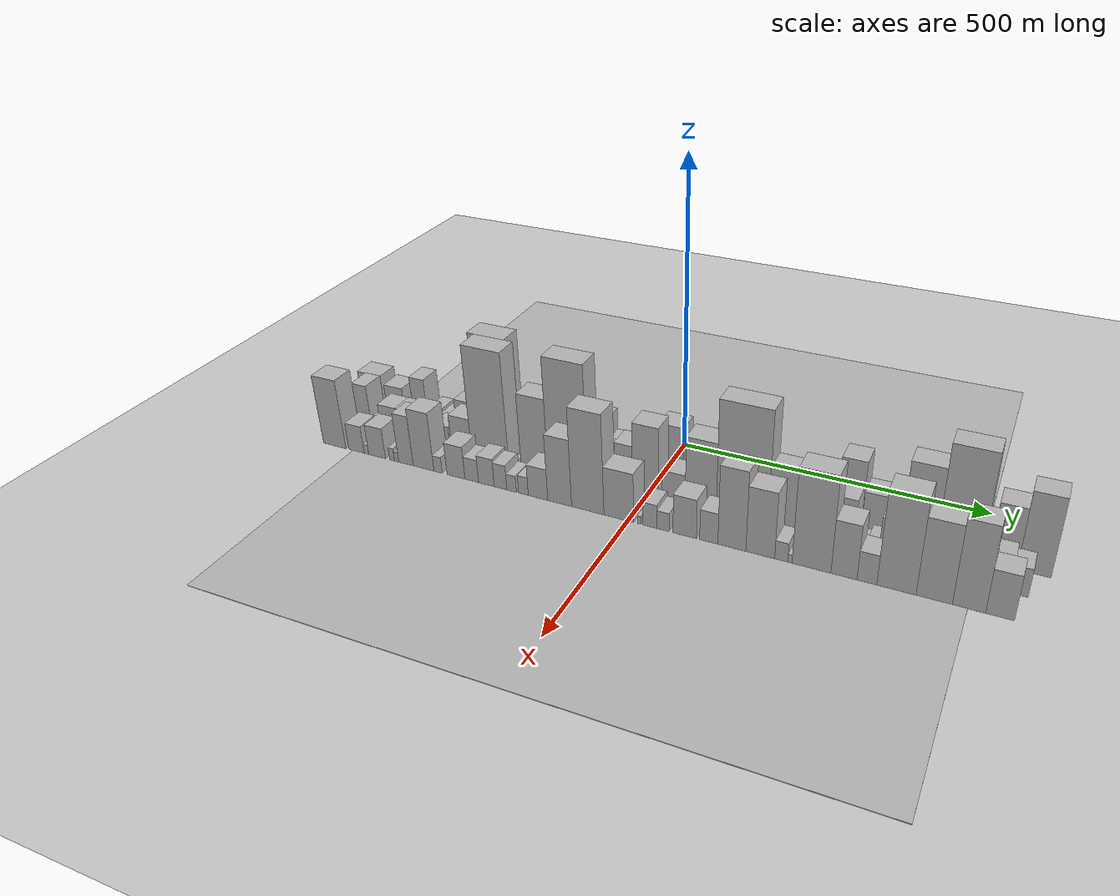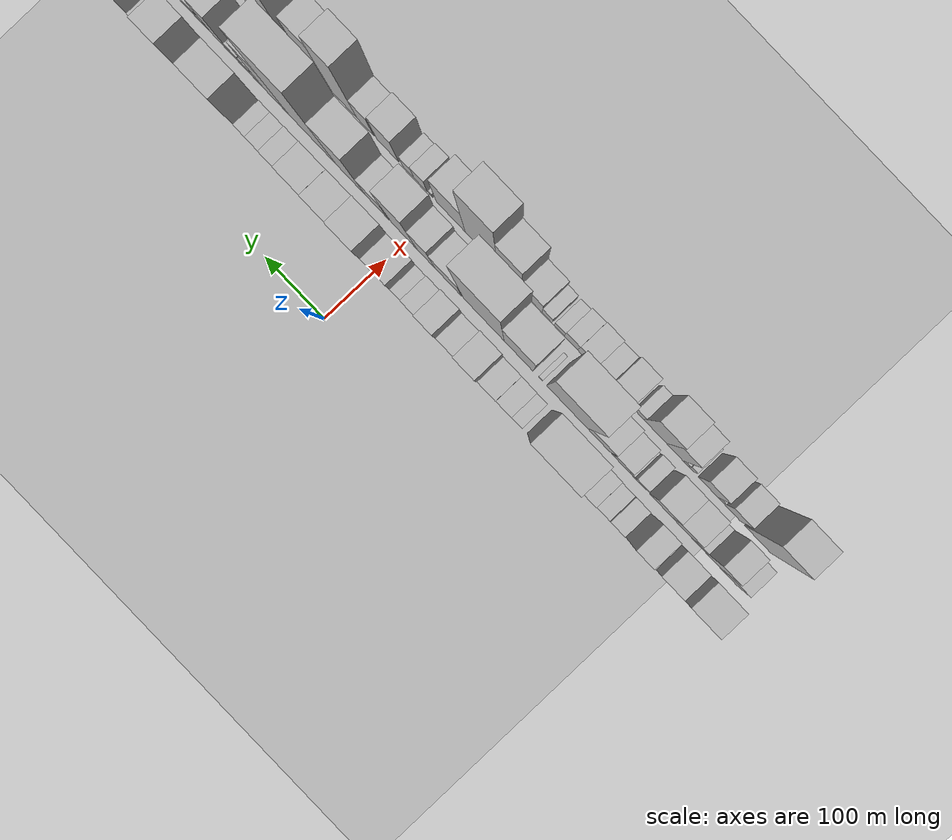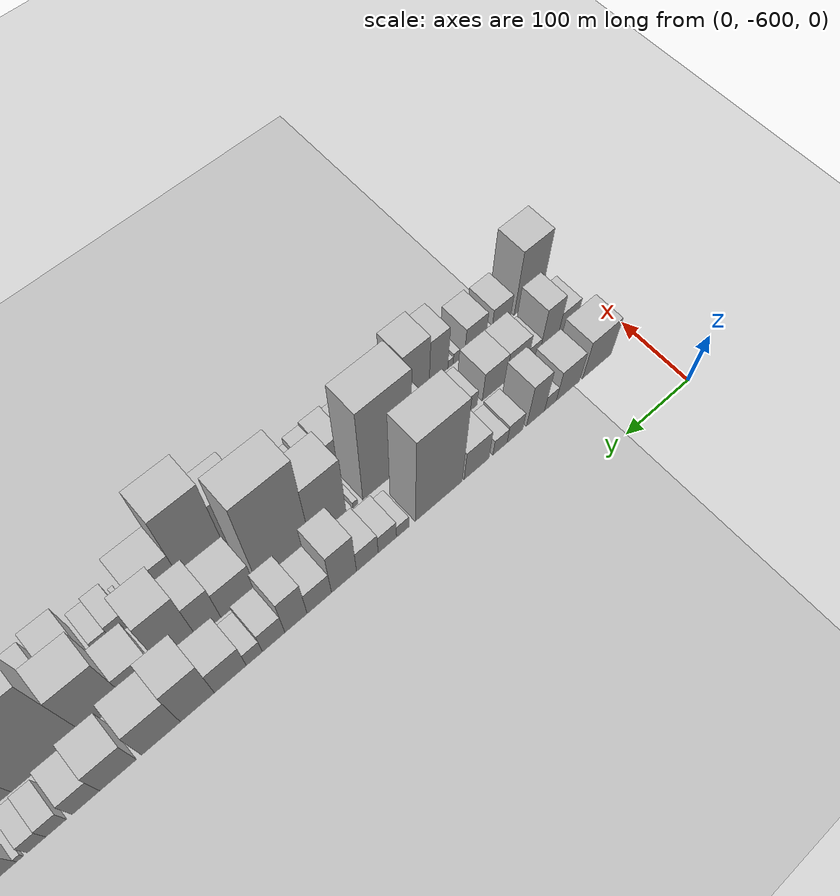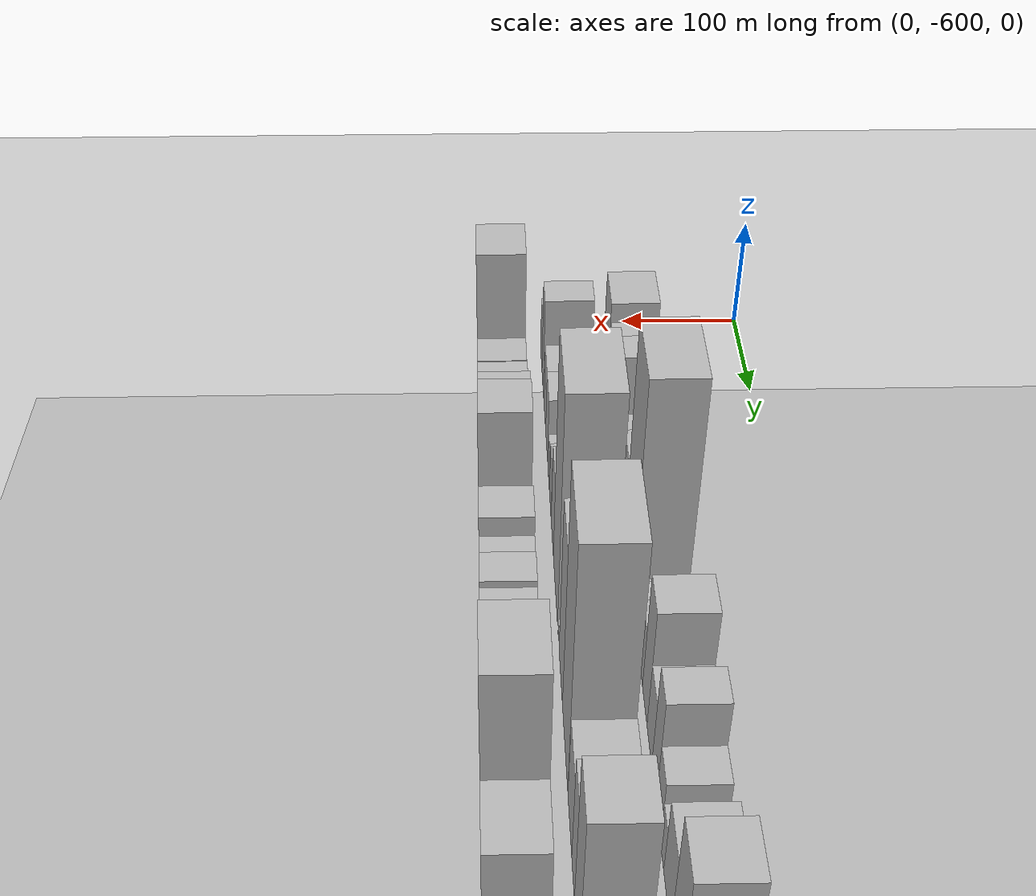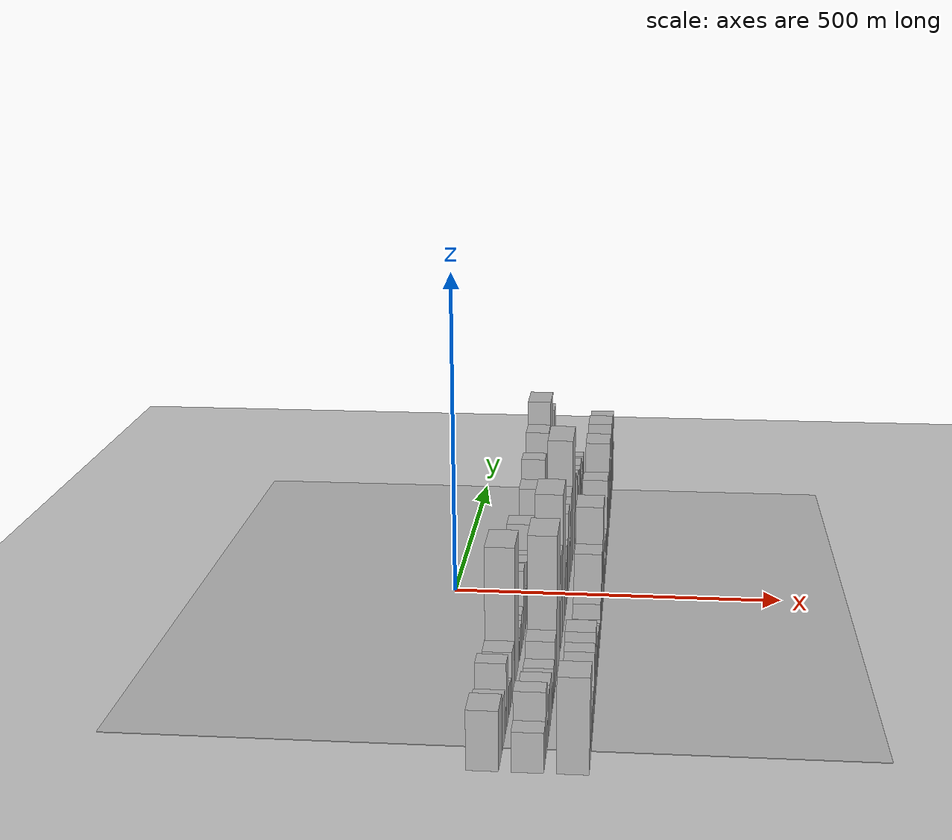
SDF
<?xml version="1.0" encoding="utf-8"?>

<sdf version="1.6">

   <world name="default">

      <gui fullscreen="0">

         <camera name="user_camera">

            <pose>-15 0 4.57585 0 0 0</pose>

            <view_controller>orbit</view_controller>

         </camera>

      </gui>

      <scene>

         <sky>

           <clouds>

             <speed>12</speed>

           </clouds>

         </sky>

         <ambient>0.4 0.4 0.4 1</ambient>

         <background>0.7 0.7 0.7 1</background>

         <shadows>1</shadows>

      </scene>

      <gravity>0 0 -9.8066</gravity>

      <magnetic_field>6e-06 2.3e-05 -4.2e-05</magnetic_field>

      <physics default="0" name="default_physics" type="ode">

         <ode>

            <solver>

               <type>quick</type>

               <iters>10</iters>

               <sor>1.0</sor>

               <use_dynamic_moi_rescaling>0</use_dynamic_moi_rescaling>

            </solver>

            <constraints>

               <cfm>0</cfm>

               <erp>0.2</erp>

               <contact_max_correcting_vel>100</contact_max_correcting_vel>

               <contact_surface_layer>0.001</contact_surface_layer>

            </constraints>

         </ode>

         <max_step_size>0.004</max_step_size>

         <real_time_factor>1</real_time_factor>

         <real_time_update_rate>250</real_time_update_rate>

      </physics>

      <light name="sun" type="directional">

         <cast_shadows>1</cast_shadows>

         <pose>0 0 10 0 0 0</pose>

         <diffuse>0.8 0.8 0.8 1</diffuse>

         <specular>0.2 0.2 0.2 1</specular>

         <attenuation>

            <range>1000</range>

            <constant>0.9</constant>

            <linear>0.01</linear>

            <quadratic>0.001</quadratic>

         </attenuation>

         <direction>-0.5 0.1 -0.9</direction>

      </light>

      <include>

         <name>ground_plane_1</name>

         <uri>model://HANNAS_ground_plane</uri>

         <pose>0 0 0  0 0 0</pose>

      </include>

      <include>

         <name>ground_plane_2</name>

         <uri>model://HANNAS_ground_plane</uri>

         <pose>100 0 0  0 0 0</pose>

      </include>

      <model name="building_1">

         <static>1</static>

         <pose frame="">100.0000 -536.6929 0 0.000000 0.000000 0.000000</pose>

         <link name="link">

            <pose frame="">0 0 40.50 0 0 0</pose>

            <collision name="collision">

               <geometry>

                  <box>

                     <size>40.0000 46.6141 81.0000</size>

                  </box>

               </geometry>

               <max_contacts>10</max_contacts>

               <surface>

                  <contact>

                     <ode/>

                  </contact>

                  <bounce/>

                  <friction>

                     <torsional>

                        <ode/>

                     </torsional>

                     <ode/>

                  </friction>

               </surface>

            </collision>

            <visual name="visual">

               <cast_shadows>0</cast_shadows>

               <geometry>

                  <box>

                     <size>40.0000 46.6141 81.0000</size>

                  </box>

               </geometry>

               <material>

                  <script>

                     <uri>model://HANNAS_wall/materials/scripts</uri>

                     <uri>model://HANNAS_wall/materials/textures</uri>

                     <name>vrc/HANNAS_wall</name>

                  </script>

               </material>

            </visual>

            <self_collide>0</self_collide>

            <enable_wind>0</enable_wind>

            <kinematic>0</kinematic>

         </link>

      </model>

      <model name="building_2">

         <static>1</static>

         <pose frame="">100.0000 -490.0142 0 0.000000 0.000000 0.000000</pose>

         <link name="link">

            <pose frame="">0 0 33.00 0 0 0</pose>

            <collision name="collision">

               <geometry>

                  <box>

                     <size>40.0000 36.7435 66.0000</size>

                  </box>

               </geometry>

               <max_contacts>10</max_contacts>

               <surface>

                  <contact>

                     <ode/>

                  </contact>

                  <bounce/>

                  <friction>

                     <torsional>

                        <ode/>

                     </torsional>

                     <ode/>

                  </friction>

               </surface>

            </collision>

            <visual name="visual">

               <cast_shadows>0</cast_shadows>

               <geometry>

                  <box>

                     <size>40.0000 36.7435 66.0000</size>

                  </box>

               </geometry>

               <material>

                  <script>

                     <uri>model://HANNAS_wall/materials/scripts</uri>

                     <uri>model://HANNAS_wall/materials/textures</uri>

                     <name>vrc/HANNAS_wall</name>

                  </script>

               </material>

            </visual>

            <self_collide>0</self_collide>

            <enable_wind>0</enable_wind>

            <kinematic>0</kinematic>

         </link>

      </model>

      <model name="building_3">

         <static>1</static>

         <pose frame="">100.0000 -462.4300 0 0.000000 0.000000 0.000000</pose>

         <link name="link">

            <pose frame="">0 0 16.50 0 0 0</pose>

            <collision name="collision">

               <geometry>

                  <box>

                     <size>40.0000 18.4248 33.0000</size>

                  </box>

               </geometry>

               <max_contacts>10</max_contacts>

               <surface>

                  <contact>

                     <ode/>

                  </contact>

                  <bounce/>

                  <friction>

                     <torsional>

                        <ode/>

                     </torsional>

                     <ode/>

                  </friction>

               </surface>

            </collision>

            <visual name="visual">

               <cast_shadows>0</cast_shadows>

               <geometry>

                  <box>

                     <size>40.0000 18.4248 33.0000</size>

                  </box>

               </geometry>

               <material>

                  <script>

                     <uri>model://HANNAS_wall/materials/scripts</uri>

                     <uri>model://HANNAS_wall/materials/textures</uri>

                     <name>vrc/HANNAS_wall</name>

                  </script>

               </material>

            </visual>

            <self_collide>0</self_collide>

            <enable_wind>0</enable_wind>

            <kinematic>0</kinematic>

         </link>

      </model>

      <model name="building_4">

         <static>1</static>

         <pose frame="">100.0000 -439.2274 0 0.000000 0.000000 0.000000</pose>

         <link name="link">

            <pose frame="">0 0 46.50 0 0 0</pose>

            <collision name="collision">

               <geometry>

                  <box>

                     <size>40.0000 27.9805 93.0000</size>

                  </box>

               </geometry>

               <max_contacts>10</max_contacts>

               <surface>

                  <contact>

                     <ode/>

                  </contact>

                  <bounce/>

                  <friction>

                     <torsional>

                        <ode/>

                     </torsional>

                     <ode/>

                  </friction>

               </surface>

            </collision>

            <visual name="visual">

               <cast_shadows>0</cast_shadows>

               <geometry>

                  <box>

                     <size>40.0000 27.9805 93.0000</size>

                  </box>

               </geometry>

               <material>

                  <script>

                     <uri>model://HANNAS_wall/materials/scripts</uri>

                     <uri>model://HANNAS_wall/materials/textures</uri>

                     <name>vrc/HANNAS_wall</name>

                  </script>

               </material>

            </visual>

            <self_collide>0</self_collide>

            <enable_wind>0</enable_wind>

            <kinematic>0</kinematic>

         </link>

      </model>

      <model name="building_5">

         <static>1</static>

         <pose frame="">100.0000 -407.3929 0 0.000000 0.000000 0.000000</pose>

         <link name="link">

            <pose frame="">0 0 21.00 0 0 0</pose>

            <collision name="collision">

               <geometry>

                  <box>

                     <size>40.0000 23.6884 42.0000</size>

                  </box>

               </geometry>

               <max_contacts>10</max_contacts>

               <surface>

                  <contact>

                     <ode/>

                  </contact>

                  <bounce/>

                  <friction>

                     <torsional>

                        <ode/>

                     </torsional>

                     <ode/>

                  </friction>

               </surface>

            </collision>

            <visual name="visual">

               <cast_shadows>0</cast_shadows>

               <geometry>

                  <box>

                     <size>40.0000 23.6884 42.0000</size>

                  </box>

               </geometry>

               <material>

                  <script>

                     <uri>model://HANNAS_wall/materials/scripts</uri>

                     <uri>model://HANNAS_wall/materials/textures</uri>

                     <name>vrc/HANNAS_wall</name>

                  </script>

               </material>

            </visual>

            <self_collide>0</self_collide>

            <enable_wind>0</enable_wind>

            <kinematic>0</kinematic>

         </link>

      </model>

      <model name="building_6">

         <static>1</static>

         <pose frame="">100.0000 -384.8416 0 0.000000 0.000000 0.000000</pose>

         <link name="link">

            <pose frame="">0 0 18.00 0 0 0</pose>

            <collision name="collision">

               <geometry>

                  <box>

                     <size>40.0000 21.4141 36.0000</size>

                  </box>

               </geometry>

               <max_contacts>10</max_contacts>

               <surface>

                  <contact>

                     <ode/>

                  </contact>

                  <bounce/>

                  <friction>

                     <torsional>

                        <ode/>

                     </torsional>

                     <ode/>

                  </friction>

               </surface>

            </collision>

            <visual name="visual">

               <cast_shadows>0</cast_shadows>

               <geometry>

                  <box>

                     <size>40.0000 21.4141 36.0000</size>

                  </box>

               </geometry>

               <material>

                  <script>

                     <uri>model://HANNAS_wall/materials/scripts</uri>

                     <uri>model://HANNAS_wall/materials/textures</uri>

                     <name>vrc/HANNAS_wall</name>

                  </script>

               </material>

            </visual>

            <self_collide>0</self_collide>

            <enable_wind>0</enable_wind>

            <kinematic>0</kinematic>

         </link>

      </model>

      <model name="building_7">

         <static>1</static>

         <pose frame="">100.0000 -349.7798 0 0.000000 0.000000 0.000000</pose>

         <link name="link">

            <pose frame="">0 0 34.50 0 0 0</pose>

            <collision name="collision">

               <geometry>

                  <box>

                     <size>40.0000 36.7094 69.0000</size>

                  </box>

               </geometry>

               <max_contacts>10</max_contacts>

               <surface>

                  <contact>

                     <ode/>

                  </contact>

                  <bounce/>

                  <friction>

                     <torsional>

                        <ode/>

                     </torsional>

                     <ode/>

                  </friction>

               </surface>

            </collision>

            <visual name="visual">

               <cast_shadows>0</cast_shadows>

               <geometry>

                  <box>

                     <size>40.0000 36.7094 69.0000</size>

                  </box>

               </geometry>

               <material>

                  <script>

                     <uri>model://HANNAS_wall/materials/scripts</uri>

                     <uri>model://HANNAS_wall/materials/textures</uri>

                     <name>vrc/HANNAS_wall</name>

                  </script>

               </material>

            </visual>

            <self_collide>0</self_collide>

            <enable_wind>0</enable_wind>

            <kinematic>0</kinematic>

         </link>

      </model>

      <model name="building_8">

         <static>1</static>

         <pose frame="">100.0000 -294.7436 0 0.000000 0.000000 0.000000</pose>

         <link name="link">

            <pose frame="">0 0 100.50 0 0 0</pose>

            <collision name="collision">

               <geometry>

                  <box>

                     <size>40.0000 67.3630 201.0000</size>

                  </box>

               </geometry>

               <max_contacts>10</max_contacts>

               <surface>

                  <contact>

                     <ode/>

                  </contact>

                  <bounce/>

                  <friction>

                     <torsional>

                        <ode/>

                     </torsional>

                     <ode/>

                  </friction>

               </surface>

            </collision>

            <visual name="visual">

               <cast_shadows>0</cast_shadows>

               <geometry>

                  <box>

                     <size>40.0000 67.3630 201.0000</size>

                  </box>

               </geometry>

               <material>

                  <script>

                     <uri>model://HANNAS_wall/materials/scripts</uri>

                     <uri>model://HANNAS_wall/materials/textures</uri>

                     <name>vrc/HANNAS_wall</name>

                  </script>

               </material>

            </visual>

            <self_collide>0</self_collide>

            <enable_wind>0</enable_wind>

            <kinematic>0</kinematic>

         </link>

      </model>

      <model name="building_9">

         <static>1</static>

         <pose frame="">100.0000 -243.3653 0 0.000000 0.000000 0.000000</pose>

         <link name="link">

            <pose frame="">0 0 15.00 0 0 0</pose>

            <collision name="collision">

               <geometry>

                  <box>

                     <size>40.0000 17.3937 30.0000</size>

                  </box>

               </geometry>

               <max_contacts>10</max_contacts>

               <surface>

                  <contact>

                     <ode/>

                  </contact>

                  <bounce/>

                  <friction>

                     <torsional>

                        <ode/>

                     </torsional>

                     <ode/>

                  </friction>

               </surface>

            </collision>

            <visual name="visual">

               <cast_shadows>0</cast_shadows>

               <geometry>

                  <box>

                     <size>40.0000 17.3937 30.0000</size>

                  </box>

               </geometry>

               <material>

                  <script>

                     <uri>model://HANNAS_wall/materials/scripts</uri>

                     <uri>model://HANNAS_wall/materials/textures</uri>

                     <name>vrc/HANNAS_wall</name>

                  </script>

               </material>

            </visual>

            <self_collide>0</self_collide>

            <enable_wind>0</enable_wind>

            <kinematic>0</kinematic>

         </link>

      </model>

      <model name="building_10">

         <static>1</static>

         <pose frame="">100.0000 -221.9480 0 0.000000 0.000000 0.000000</pose>

         <link name="link">

            <pose frame="">0 0 22.50 0 0 0</pose>

            <collision name="collision">

               <geometry>

                  <box>

                     <size>40.0000 25.4409 45.0000</size>

                  </box>

               </geometry>

               <max_contacts>10</max_contacts>

               <surface>

                  <contact>

                     <ode/>

                  </contact>

                  <bounce/>

                  <friction>

                     <torsional>

                        <ode/>

                     </torsional>

                     <ode/>

                  </friction>

               </surface>

            </collision>

            <visual name="visual">

               <cast_shadows>0</cast_shadows>

               <geometry>

                  <box>

                     <size>40.0000 25.4409 45.0000</size>

                  </box>

               </geometry>

               <material>

                  <script>

                     <uri>model://HANNAS_wall/materials/scripts</uri>

                     <uri>model://HANNAS_wall/materials/textures</uri>

                     <name>vrc/HANNAS_wall</name>

                  </script>

               </material>

            </visual>

            <self_collide>0</self_collide>

            <enable_wind>0</enable_wind>

            <kinematic>0</kinematic>

         </link>

      </model>

      <model name="building_11">

         <static>1</static>

         <pose frame="">100.0000 -194.4827 0 0.000000 0.000000 0.000000</pose>

         <link name="link">

            <pose frame="">0 0 27.00 0 0 0</pose>

            <collision name="collision">

               <geometry>

                  <box>

                     <size>40.0000 29.4895 54.0000</size>

                  </box>

               </geometry>

               <max_contacts>10</max_contacts>

               <surface>

                  <contact>

                     <ode/>

                  </contact>

                  <bounce/>

                  <friction>

                     <torsional>

                        <ode/>

                     </torsional>

                     <ode/>

                  </friction>

               </surface>

            </collision>

            <visual name="visual">

               <cast_shadows>0</cast_shadows>

               <geometry>

                  <box>

                     <size>40.0000 29.4895 54.0000</size>

                  </box>

               </geometry>

               <material>

                  <script>

                     <uri>model://HANNAS_wall/materials/scripts</uri>

                     <uri>model://HANNAS_wall/materials/textures</uri>

                     <name>vrc/HANNAS_wall</name>

                  </script>

               </material>

            </visual>

            <self_collide>0</self_collide>

            <enable_wind>0</enable_wind>

            <kinematic>0</kinematic>

         </link>

      </model>

      <model name="building_12">

         <static>1</static>

         <pose frame="">100.0000 -162.9726 0 0.000000 0.000000 0.000000</pose>

         <link name="link">

            <pose frame="">0 0 54.00 0 0 0</pose>

            <collision name="collision">

               <geometry>

                  <box>

                     <size>40.0000 33.5308 108.0000</size>

                  </box>

               </geometry>

               <max_contacts>10</max_contacts>

               <surface>

                  <contact>

                     <ode/>

                  </contact>

                  <bounce/>

                  <friction>

                     <torsional>

                        <ode/>

                     </torsional>

                     <ode/>

                  </friction>

               </surface>

            </collision>

            <visual name="visual">

               <cast_shadows>0</cast_shadows>

               <geometry>

                  <box>

                     <size>40.0000 33.5308 108.0000</size>

                  </box>

               </geometry>

               <material>

                  <script>

                     <uri>model://HANNAS_wall/materials/scripts</uri>

                     <uri>model://HANNAS_wall/materials/textures</uri>

                     <name>vrc/HANNAS_wall</name>

                  </script>

               </material>

            </visual>

            <self_collide>0</self_collide>

            <enable_wind>0</enable_wind>

            <kinematic>0</kinematic>

         </link>

      </model>

      <model name="building_13">

         <static>1</static>

         <pose frame="">100.0000 -130.0925 0 0.000000 0.000000 0.000000</pose>

         <link name="link">

            <pose frame="">0 0 30.00 0 0 0</pose>

            <collision name="collision">

               <geometry>

                  <box>

                     <size>40.0000 32.2293 60.0000</size>

                  </box>

               </geometry>

               <max_contacts>10</max_contacts>

               <surface>

                  <contact>

                     <ode/>

                  </contact>

                  <bounce/>

                  <friction>

                     <torsional>

                        <ode/>

                     </torsional>

                     <ode/>

                  </friction>

               </surface>

            </collision>

            <visual name="visual">

               <cast_shadows>0</cast_shadows>

               <geometry>

                  <box>

                     <size>40.0000 32.2293 60.0000</size>

                  </box>

               </geometry>

               <material>

                  <script>

                     <uri>model://HANNAS_wall/materials/scripts</uri>

                     <uri>model://HANNAS_wall/materials/textures</uri>

                     <name>vrc/HANNAS_wall</name>

                  </script>

               </material>

            </visual>

            <self_collide>0</self_collide>

            <enable_wind>0</enable_wind>

            <kinematic>0</kinematic>

         </link>

      </model>

      <model name="building_14">

         <static>1</static>

         <pose frame="">100.0000 -99.5629 0 0.000000 0.000000 0.000000</pose>

         <link name="link">

            <pose frame="">0 0 48.00 0 0 0</pose>

            <collision name="collision">

               <geometry>

                  <box>

                     <size>40.0000 28.8300 96.0000</size>

                  </box>

               </geometry>

               <max_contacts>10</max_contacts>

               <surface>

                  <contact>

                     <ode/>

                  </contact>

                  <bounce/>

                  <friction>

                     <torsional>

                        <ode/>

                     </torsional>

                     <ode/>

                  </friction>

               </surface>

            </collision>

            <visual name="visual">

               <cast_shadows>0</cast_shadows>

               <geometry>

                  <box>

                     <size>40.0000 28.8300 96.0000</size>

                  </box>

               </geometry>

               <material>

                  <script>

                     <uri>model://HANNAS_wall/materials/scripts</uri>

                     <uri>model://HANNAS_wall/materials/textures</uri>

                     <name>vrc/HANNAS_wall</name>

                  </script>

               </material>

            </visual>

            <self_collide>0</self_collide>

            <enable_wind>0</enable_wind>

            <kinematic>0</kinematic>

         </link>

      </model>

      <model name="building_15">

         <static>1</static>

         <pose frame="">100.0000 -70.8435 0 0.000000 0.000000 0.000000</pose>

         <link name="link">

            <pose frame="">0 0 28.50 0 0 0</pose>

            <collision name="collision">

               <geometry>

                  <box>

                     <size>40.0000 28.6087 57.0000</size>

                  </box>

               </geometry>

               <max_contacts>10</max_contacts>

               <surface>

                  <contact>

                     <ode/>

                  </contact>

                  <bounce/>

                  <friction>

                     <torsional>

                        <ode/>

                     </torsional>

                     <ode/>

                  </friction>

               </surface>

            </collision>

            <visual name="visual">

               <cast_shadows>0</cast_shadows>

               <geometry>

                  <box>

                     <size>40.0000 28.6087 57.0000</size>

                  </box>

               </geometry>

               <material>

                  <script>

                     <uri>model://HANNAS_wall/materials/scripts</uri>

                     <uri>model://HANNAS_wall/materials/textures</uri>

                     <name>vrc/HANNAS_wall</name>

                  </script>

               </material>

            </visual>

            <self_collide>0</self_collide>

            <enable_wind>0</enable_wind>

            <kinematic>0</kinematic>

         </link>

      </model>

      <model name="building_16">

         <static>1</static>

         <pose frame="">100.0000 -46.3662 0 0.000000 0.000000 0.000000</pose>

         <link name="link">

            <pose frame="">0 0 19.50 0 0 0</pose>

            <collision name="collision">

               <geometry>

                  <box>

                     <size>40.0000 20.3460 39.0000</size>

                  </box>

               </geometry>

               <max_contacts>10</max_contacts>

               <surface>

                  <contact>

                     <ode/>

                  </contact>

                  <bounce/>

                  <friction>

                     <torsional>

                        <ode/>

                     </torsional>

                     <ode/>

                  </friction>

               </surface>

            </collision>

            <visual name="visual">

               <cast_shadows>0</cast_shadows>

               <geometry>

                  <box>

                     <size>40.0000 20.3460 39.0000</size>

                  </box>

               </geometry>

               <material>

                  <script>

                     <uri>model://HANNAS_wall/materials/scripts</uri>

                     <uri>model://HANNAS_wall/materials/textures</uri>

                     <name>vrc/HANNAS_wall</name>

                  </script>

               </material>

            </visual>

            <self_collide>0</self_collide>

            <enable_wind>0</enable_wind>

            <kinematic>0</kinematic>

         </link>

      </model>

      <model name="building_17">

         <static>1</static>

         <pose frame="">100.0000 -16.3731 0 0.000000 0.000000 0.000000</pose>

         <link name="link">

            <pose frame="">0 0 34.50 0 0 0</pose>

            <collision name="collision">

               <geometry>

                  <box>

                     <size>40.0000 39.6402 69.0000</size>

                  </box>

               </geometry>

               <max_contacts>10</max_contacts>

               <surface>

                  <contact>

                     <ode/>

                  </contact>

                  <bounce/>

                  <friction>

                     <torsional>

                        <ode/>

                     </torsional>

                     <ode/>

                  </friction>

               </surface>

            </collision>

            <visual name="visual">

               <cast_shadows>0</cast_shadows>

               <geometry>

                  <box>

                     <size>40.0000 39.6402 69.0000</size>

                  </box>

               </geometry>

               <material>

                  <script>

                     <uri>model://HANNAS_wall/materials/scripts</uri>

                     <uri>model://HANNAS_wall/materials/textures</uri>

                     <name>vrc/HANNAS_wall</name>

                  </script>

               </material>

            </visual>

            <self_collide>0</self_collide>

            <enable_wind>0</enable_wind>

            <kinematic>0</kinematic>

         </link>

      </model>

      <model name="building_18">

         <static>1</static>

         <pose frame="">100.0000 24.0642 0 0.000000 0.000000 0.000000</pose>

         <link name="link">

            <pose frame="">0 0 55.50 0 0 0</pose>

            <collision name="collision">

               <geometry>

                  <box>

                     <size>40.0000 41.2345 111.0000</size>

                  </box>

               </geometry>

               <max_contacts>10</max_contacts>

               <surface>

                  <contact>

                     <ode/>

                  </contact>

                  <bounce/>

                  <friction>

                     <torsional>

                        <ode/>

                     </torsional>

                     <ode/>

                  </friction>

               </surface>

            </collision>

            <visual name="visual">

               <cast_shadows>0</cast_shadows>

               <geometry>

                  <box>

                     <size>40.0000 41.2345 111.0000</size>

                  </box>

               </geometry>

               <material>

                  <script>

                     <uri>model://HANNAS_wall/materials/scripts</uri>

                     <uri>model://HANNAS_wall/materials/textures</uri>

                     <name>vrc/HANNAS_wall</name>

                  </script>

               </material>

            </visual>

            <self_collide>0</self_collide>

            <enable_wind>0</enable_wind>

            <kinematic>0</kinematic>

         </link>

      </model>

      <model name="building_19">

         <static>1</static>

         <pose frame="">100.0000 67.6600 0 0.000000 0.000000 0.000000</pose>

         <link name="link">

            <pose frame="">0 0 45.00 0 0 0</pose>

            <collision name="collision">

               <geometry>

                  <box>

                     <size>40.0000 45.9570 90.0000</size>

                  </box>

               </geometry>

               <max_contacts>10</max_contacts>

               <surface>

                  <contact>

                     <ode/>

                  </contact>

                  <bounce/>

                  <friction>

                     <torsional>

                        <ode/>

                     </torsional>

                     <ode/>

                  </friction>

               </surface>

            </collision>

            <visual name="visual">

               <cast_shadows>0</cast_shadows>

               <geometry>

                  <box>

                     <size>40.0000 45.9570 90.0000</size>

                  </box>

               </geometry>

               <material>

                  <script>

                     <uri>model://HANNAS_wall/materials/scripts</uri>

                     <uri>model://HANNAS_wall/materials/textures</uri>

                     <name>vrc/HANNAS_wall</name>

                  </script>

               </material>

            </visual>

            <self_collide>0</self_collide>

            <enable_wind>0</enable_wind>

            <kinematic>0</kinematic>

         </link>

      </model>

      <model name="building_20">

         <static>1</static>

         <pose frame="">100.0000 117.6161 0 0.000000 0.000000 0.000000</pose>

         <link name="link">

            <pose frame="">0 0 37.50 0 0 0</pose>

            <collision name="collision">

               <geometry>

                  <box>

                     <size>40.0000 41.9552 75.0000</size>

                  </box>

               </geometry>

               <max_contacts>10</max_contacts>

               <surface>

                  <contact>

                     <ode/>

                  </contact>

                  <bounce/>

                  <friction>

                     <torsional>

                        <ode/>

                     </torsional>

                     <ode/>

                  </friction>

               </surface>

            </collision>

            <visual name="visual">

               <cast_shadows>0</cast_shadows>

               <geometry>

                  <box>

                     <size>40.0000 41.9552 75.0000</size>

                  </box>

               </geometry>

               <material>

                  <script>

                     <uri>model://HANNAS_wall/materials/scripts</uri>

                     <uri>model://HANNAS_wall/materials/textures</uri>

                     <name>vrc/HANNAS_wall</name>

                  </script>

               </material>

            </visual>

            <self_collide>0</self_collide>

            <enable_wind>0</enable_wind>

            <kinematic>0</kinematic>

         </link>

      </model>

      <model name="building_21">

         <static>1</static>

         <pose frame="">100.0000 154.2521 0 0.000000 0.000000 0.000000</pose>

         <link name="link">

            <pose frame="">0 0 28.50 0 0 0</pose>

            <collision name="collision">

               <geometry>

                  <box>

                     <size>40.0000 31.3169 57.0000</size>

                  </box>

               </geometry>

               <max_contacts>10</max_contacts>

               <surface>

                  <contact>

                     <ode/>

                  </contact>

                  <bounce/>

                  <friction>

                     <torsional>

                        <ode/>

                     </torsional>

                     <ode/>

                  </friction>

               </surface>

            </collision>

            <visual name="visual">

               <cast_shadows>0</cast_shadows>

               <geometry>

                  <box>

                     <size>40.0000 31.3169 57.0000</size>

                  </box>

               </geometry>

               <material>

                  <script>

                     <uri>model://HANNAS_wall/materials/scripts</uri>

                     <uri>model://HANNAS_wall/materials/textures</uri>

                     <name>vrc/HANNAS_wall</name>

                  </script>

               </material>

            </visual>

            <self_collide>0</self_collide>

            <enable_wind>0</enable_wind>

            <kinematic>0</kinematic>

         </link>

      </model>

      <model name="building_22">

         <static>1</static>

         <pose frame="">100.0000 187.3715 0 0.000000 0.000000 0.000000</pose>

         <link name="link">

            <pose frame="">0 0 21.00 0 0 0</pose>

            <collision name="collision">

               <geometry>

                  <box>

                     <size>40.0000 22.9218 42.0000</size>

                  </box>

               </geometry>

               <max_contacts>10</max_contacts>

               <surface>

                  <contact>

                     <ode/>

                  </contact>

                  <bounce/>

                  <friction>

                     <torsional>

                        <ode/>

                     </torsional>

                     <ode/>

                  </friction>

               </surface>

            </collision>

            <visual name="visual">

               <cast_shadows>0</cast_shadows>

               <geometry>

                  <box>

                     <size>40.0000 22.9218 42.0000</size>

                  </box>

               </geometry>

               <material>

                  <script>

                     <uri>model://HANNAS_wall/materials/scripts</uri>

                     <uri>model://HANNAS_wall/materials/textures</uri>

                     <name>vrc/HANNAS_wall</name>

                  </script>

               </material>

            </visual>

            <self_collide>0</self_collide>

            <enable_wind>0</enable_wind>

            <kinematic>0</kinematic>

         </link>

      </model>

      <model name="building_23">

         <static>1</static>

         <pose frame="">100.0000 208.8931 0 0.000000 0.000000 0.000000</pose>

         <link name="link">

            <pose frame="">0 0 19.50 0 0 0</pose>

            <collision name="collision">

               <geometry>

                  <box>

                     <size>40.0000 20.1214 39.0000</size>

                  </box>

               </geometry>

               <max_contacts>10</max_contacts>

               <surface>

                  <contact>

                     <ode/>

                  </contact>

                  <bounce/>

                  <friction>

                     <torsional>

                        <ode/>

                     </torsional>

                     <ode/>

                  </friction>

               </surface>

            </collision>

            <visual name="visual">

               <cast_shadows>0</cast_shadows>

               <geometry>

                  <box>

                     <size>40.0000 20.1214 39.0000</size>

                  </box>

               </geometry>

               <material>

                  <script>

                     <uri>model://HANNAS_wall/materials/scripts</uri>

                     <uri>model://HANNAS_wall/materials/textures</uri>

                     <name>vrc/HANNAS_wall</name>

                  </script>

               </material>

            </visual>

            <self_collide>0</self_collide>

            <enable_wind>0</enable_wind>

            <kinematic>0</kinematic>

         </link>

      </model>

      <model name="building_24">

         <static>1</static>

         <pose frame="">100.0000 226.6315 0 0.000000 0.000000 0.000000</pose>

         <link name="link">

            <pose frame="">0 0 7.50 0 0 0</pose>

            <collision name="collision">

               <geometry>

                  <box>

                     <size>40.0000 7.3554 15.0000</size>

                  </box>

               </geometry>

               <max_contacts>10</max_contacts>

               <surface>

                  <contact>

                     <ode/>

                  </contact>

                  <bounce/>

                  <friction>

                     <torsional>

                        <ode/>

                     </torsional>

                     <ode/>

                  </friction>

               </surface>

            </collision>

            <visual name="visual">

               <cast_shadows>0</cast_shadows>

               <geometry>

                  <box>

                     <size>40.0000 7.3554 15.0000</size>

                  </box>

               </geometry>

               <material>

                  <script>

                     <uri>model://HANNAS_wall/materials/scripts</uri>

                     <uri>model://HANNAS_wall/materials/textures</uri>

                     <name>vrc/HANNAS_wall</name>

                  </script>

               </material>

            </visual>

            <self_collide>0</self_collide>

            <enable_wind>0</enable_wind>

            <kinematic>0</kinematic>

         </link>

      </model>

      <model name="building_25">

         <static>1</static>

         <pose frame="">100.0000 256.3185 0 0.000000 0.000000 0.000000</pose>

         <link name="link">

            <pose frame="">0 0 45.00 0 0 0</pose>

            <collision name="collision">

               <geometry>

                  <box>

                     <size>40.0000 52.0186 90.0000</size>

                  </box>

               </geometry>

               <max_contacts>10</max_contacts>

               <surface>

                  <contact>

                     <ode/>

                  </contact>

                  <bounce/>

                  <friction>

                     <torsional>

                        <ode/>

                     </torsional>

                     <ode/>

                  </friction>

               </surface>

            </collision>

            <visual name="visual">

               <cast_shadows>0</cast_shadows>

               <geometry>

                  <box>

                     <size>40.0000 52.0186 90.0000</size>

                  </box>

               </geometry>

               <material>

                  <script>

                     <uri>model://HANNAS_wall/materials/scripts</uri>

                     <uri>model://HANNAS_wall/materials/textures</uri>

                     <name>vrc/HANNAS_wall</name>

                  </script>

               </material>

            </visual>

            <self_collide>0</self_collide>

            <enable_wind>0</enable_wind>

            <kinematic>0</kinematic>

         </link>

      </model>

      <model name="building_26">

         <static>1</static>

         <pose frame="">100.0000 308.2832 0 0.000000 0.000000 0.000000</pose>

         <link name="link">

            <pose frame="">0 0 61.50 0 0 0</pose>

            <collision name="collision">

               <geometry>

                  <box>

                     <size>40.0000 37.9109 123.0000</size>

                  </box>

               </geometry>

               <max_contacts>10</max_contacts>

               <surface>

                  <contact>

                     <ode/>

                  </contact>

                  <bounce/>

                  <friction>

                     <torsional>

                        <ode/>

                     </torsional>

                     <ode/>

                  </friction>

               </surface>

            </collision>

            <visual name="visual">

               <cast_shadows>0</cast_shadows>

               <geometry>

                  <box>

                     <size>40.0000 37.9109 123.0000</size>

                  </box>

               </geometry>

               <material>

                  <script>

                     <uri>model://HANNAS_wall/materials/scripts</uri>

                     <uri>model://HANNAS_wall/materials/textures</uri>

                     <name>vrc/HANNAS_wall</name>

                  </script>

               </material>

            </visual>

            <self_collide>0</self_collide>

            <enable_wind>0</enable_wind>

            <kinematic>0</kinematic>

         </link>

      </model>

      <model name="building_27">

         <static>1</static>

         <pose frame="">100.0000 347.2899 0 0.000000 0.000000 0.000000</pose>

         <link name="link">

            <pose frame="">0 0 36.00 0 0 0</pose>

            <collision name="collision">

               <geometry>

                  <box>

                     <size>40.0000 40.1024 72.0000</size>

                  </box>

               </geometry>

               <max_contacts>10</max_contacts>

               <surface>

                  <contact>

                     <ode/>

                  </contact>

                  <bounce/>

                  <friction>

                     <torsional>

                        <ode/>

                     </torsional>

                     <ode/>

                  </friction>

               </surface>

            </collision>

            <visual name="visual">

               <cast_shadows>0</cast_shadows>

               <geometry>

                  <box>

                     <size>40.0000 40.1024 72.0000</size>

                  </box>

               </geometry>

               <material>

                  <script>

                     <uri>model://HANNAS_wall/materials/scripts</uri>

                     <uri>model://HANNAS_wall/materials/textures</uri>

                     <name>vrc/HANNAS_wall</name>

                  </script>

               </material>

            </visual>

            <self_collide>0</self_collide>

            <enable_wind>0</enable_wind>

            <kinematic>0</kinematic>

         </link>

      </model>

      <model name="building_28">

         <static>1</static>

         <pose frame="">100.0000 376.7206 0 0.000000 0.000000 0.000000</pose>

         <link name="link">

            <pose frame="">0 0 18.00 0 0 0</pose>

            <collision name="collision">

               <geometry>

                  <box>

                     <size>40.0000 18.7589 36.0000</size>

                  </box>

               </geometry>

               <max_contacts>10</max_contacts>

               <surface>

                  <contact>

                     <ode/>

                  </contact>

                  <bounce/>

                  <friction>

                     <torsional>

                        <ode/>

                     </torsional>

                     <ode/>

                  </friction>

               </surface>

            </collision>

            <visual name="visual">

               <cast_shadows>0</cast_shadows>

               <geometry>

                  <box>

                     <size>40.0000 18.7589 36.0000</size>

                  </box>

               </geometry>

               <material>

                  <script>

                     <uri>model://HANNAS_wall/materials/scripts</uri>

                     <uri>model://HANNAS_wall/materials/textures</uri>

                     <name>vrc/HANNAS_wall</name>

                  </script>

               </material>

            </visual>

            <self_collide>0</self_collide>

            <enable_wind>0</enable_wind>

            <kinematic>0</kinematic>

         </link>

      </model>

      <model name="building_29">

         <static>1</static>

         <pose frame="">100.0000 411.4911 0 0.000000 0.000000 0.000000</pose>

         <link name="link">

            <pose frame="">0 0 70.50 0 0 0</pose>

            <collision name="collision">

               <geometry>

                  <box>

                     <size>40.0000 50.7822 141.0000</size>

                  </box>

               </geometry>

               <max_contacts>10</max_contacts>

               <surface>

                  <contact>

                     <ode/>

                  </contact>

                  <bounce/>

                  <friction>

                     <torsional>

                        <ode/>

                     </torsional>

                     <ode/>

                  </friction>

               </surface>

            </collision>

            <visual name="visual">

               <cast_shadows>0</cast_shadows>

               <geometry>

                  <box>

                     <size>40.0000 50.7822 141.0000</size>

                  </box>

               </geometry>

               <material>

                  <script>

                     <uri>model://HANNAS_wall/materials/scripts</uri>

                     <uri>model://HANNAS_wall/materials/textures</uri>

                     <name>vrc/HANNAS_wall</name>

                  </script>

               </material>

            </visual>

            <self_collide>0</self_collide>

            <enable_wind>0</enable_wind>

            <kinematic>0</kinematic>

         </link>

      </model>

      <model name="building_30">

         <static>1</static>

         <pose frame="">100.0000 469.4045 0 0.000000 0.000000 0.000000</pose>

         <link name="link">

            <pose frame="">0 0 91.50 0 0 0</pose>

            <collision name="collision">

               <geometry>

                  <box>

                     <size>40.0000 65.0444 183.0000</size>

                  </box>

               </geometry>

               <max_contacts>10</max_contacts>

               <surface>

                  <contact>

                     <ode/>

                  </contact>

                  <bounce/>

                  <friction>

                     <torsional>

                        <ode/>

                     </torsional>

                     <ode/>

                  </friction>

               </surface>

            </collision>

            <visual name="visual">

               <cast_shadows>0</cast_shadows>

               <geometry>

                  <box>

                     <size>40.0000 65.0444 183.0000</size>

                  </box>

               </geometry>

               <material>

                  <script>

                     <uri>model://HANNAS_wall/materials/scripts</uri>

                     <uri>model://HANNAS_wall/materials/textures</uri>

                     <name>vrc/HANNAS_wall</name>

                  </script>

               </material>

            </visual>

            <self_collide>0</self_collide>

            <enable_wind>0</enable_wind>

            <kinematic>0</kinematic>

         </link>

      </model>

      <model name="building_31">

         <static>1</static>

         <pose frame="">100.0000 507.0279 0 0.000000 0.000000 0.000000</pose>

         <link name="link">

            <pose frame="">0 0 12.00 0 0 0</pose>

            <collision name="collision">

               <geometry>

                  <box>

                     <size>40.0000 10.2025 24.0000</size>

                  </box>

               </geometry>

               <max_contacts>10</max_contacts>

               <surface>

                  <contact>

                     <ode/>

                  </contact>

                  <bounce/>

                  <friction>

                     <torsional>

                        <ode/>

                     </torsional>

                     <ode/>

                  </friction>

               </surface>

            </collision>

            <visual name="visual">

               <cast_shadows>0</cast_shadows>

               <geometry>

                  <box>

                     <size>40.0000 10.2025 24.0000</size>

                  </box>

               </geometry>

               <material>

                  <script>

                     <uri>model://HANNAS_wall/materials/scripts</uri>

                     <uri>model://HANNAS_wall/materials/textures</uri>

                     <name>vrc/HANNAS_wall</name>

                  </script>

               </material>

            </visual>

            <self_collide>0</self_collide>

            <enable_wind>0</enable_wind>

            <kinematic>0</kinematic>

         </link>

      </model>

      <model name="building_32">

         <static>1</static>

         <pose frame="">100.0000 531.5243 0 0.000000 0.000000 0.000000</pose>

         <link name="link">

            <pose frame="">0 0 52.50 0 0 0</pose>

            <collision name="collision">

               <geometry>

                  <box>

                     <size>40.0000 38.7903 105.0000</size>

                  </box>

               </geometry>

               <max_contacts>10</max_contacts>

               <surface>

                  <contact>

                     <ode/>

                  </contact>

                  <bounce/>

                  <friction>

                     <torsional>

                        <ode/>

                     </torsional>

                     <ode/>

                  </friction>

               </surface>

            </collision>

            <visual name="visual">

               <cast_shadows>0</cast_shadows>

               <geometry>

                  <box>

                     <size>40.0000 38.7903 105.0000</size>

                  </box>

               </geometry>

               <material>

                  <script>

                     <uri>model://HANNAS_wall/materials/scripts</uri>

                     <uri>model://HANNAS_wall/materials/textures</uri>

                     <name>vrc/HANNAS_wall</name>

                  </script>

               </material>

            </visual>

            <self_collide>0</self_collide>

            <enable_wind>0</enable_wind>

            <kinematic>0</kinematic>

         </link>

      </model>

      <model name="building_33">

         <static>1</static>

         <pose frame="">100.0000 573.8433 0 0.000000 0.000000 0.000000</pose>

         <link name="link">

            <pose frame="">0 0 67.50 0 0 0</pose>

            <collision name="collision">

               <geometry>

                  <box>

                     <size>40.0000 45.8476 135.0000</size>

                  </box>

               </geometry>

               <max_contacts>10</max_contacts>

               <surface>

                  <contact>

                     <ode/>

                  </contact>

                  <bounce/>

                  <friction>

                     <torsional>

                        <ode/>

                     </torsional>

                     <ode/>

                  </friction>

               </surface>

            </collision>

            <visual name="visual">

               <cast_shadows>0</cast_shadows>

               <geometry>

                  <box>

                     <size>40.0000 45.8476 135.0000</size>

                  </box>

               </geometry>

               <material>

                  <script>

                     <uri>model://HANNAS_wall/materials/scripts</uri>

                     <uri>model://HANNAS_wall/materials/textures</uri>

                     <name>vrc/HANNAS_wall</name>

                  </script>

               </material>

            </visual>

            <self_collide>0</self_collide>

            <enable_wind>0</enable_wind>

            <kinematic>0</kinematic>

         </link>

      </model>

      <model name="building_34">

         <static>1</static>

         <pose frame="">155.0000 -544.6800 0 0.000000 0.000000 0.000000</pose>

         <link name="link">

            <pose frame="">0 0 27.00 0 0 0</pose>

            <collision name="collision">

               <geometry>

                  <box>

                     <size>40.0000 30.6399 54.0000</size>

                  </box>

               </geometry>

               <max_contacts>10</max_contacts>

               <surface>

                  <contact>

                     <ode/>

                  </contact>

                  <bounce/>

                  <friction>

                     <torsional>

                        <ode/>

                     </torsional>

                     <ode/>

                  </friction>

               </surface>

            </collision>

            <visual name="visual">

               <cast_shadows>0</cast_shadows>

               <geometry>

                  <box>

                     <size>40.0000 30.6399 54.0000</size>

                  </box>

               </geometry>

               <material>

                  <script>

                     <uri>model://HANNAS_wall/materials/scripts</uri>

                     <uri>model://HANNAS_wall/materials/textures</uri>

                     <name>vrc/HANNAS_wall</name>

                  </script>

               </material>

            </visual>

            <self_collide>0</self_collide>

            <enable_wind>0</enable_wind>

            <kinematic>0</kinematic>

         </link>

      </model>

      <model name="building_35">

         <static>1</static>

         <pose frame="">155.0000 -515.0606 0 0.000000 0.000000 0.000000</pose>

         <link name="link">

            <pose frame="">0 0 46.50 0 0 0</pose>

            <collision name="collision">

               <geometry>

                  <box>

                     <size>40.0000 28.5989 93.0000</size>

                  </box>

               </geometry>

               <max_contacts>10</max_contacts>

               <surface>

                  <contact>

                     <ode/>

                  </contact>

                  <bounce/>

                  <friction>

                     <torsional>

                        <ode/>

                     </torsional>

                     <ode/>

                  </friction>

               </surface>

            </collision>

            <visual name="visual">

               <cast_shadows>0</cast_shadows>

               <geometry>

                  <box>

                     <size>40.0000 28.5989 93.0000</size>

                  </box>

               </geometry>

               <material>

                  <script>

                     <uri>model://HANNAS_wall/materials/scripts</uri>

                     <uri>model://HANNAS_wall/materials/textures</uri>

                     <name>vrc/HANNAS_wall</name>

                  </script>

               </material>

            </visual>

            <self_collide>0</self_collide>

            <enable_wind>0</enable_wind>

            <kinematic>0</kinematic>

         </link>

      </model>

      <model name="building_36">

         <static>1</static>

         <pose frame="">155.0000 -491.3935 0 0.000000 0.000000 0.000000</pose>

         <link name="link">

            <pose frame="">0 0 16.50 0 0 0</pose>

            <collision name="collision">

               <geometry>

                  <box>

                     <size>40.0000 18.7354 33.0000</size>

                  </box>

               </geometry>

               <max_contacts>10</max_contacts>

               <surface>

                  <contact>

                     <ode/>

                  </contact>

                  <bounce/>

                  <friction>

                     <torsional>

                        <ode/>

                     </torsional>

                     <ode/>

                  </friction>

               </surface>

            </collision>

            <visual name="visual">

               <cast_shadows>0</cast_shadows>

               <geometry>

                  <box>

                     <size>40.0000 18.7354 33.0000</size>

                  </box>

               </geometry>

               <material>

                  <script>

                     <uri>model://HANNAS_wall/materials/scripts</uri>

                     <uri>model://HANNAS_wall/materials/textures</uri>

                     <name>vrc/HANNAS_wall</name>

                  </script>

               </material>

            </visual>

            <self_collide>0</self_collide>

            <enable_wind>0</enable_wind>

            <kinematic>0</kinematic>

         </link>

      </model>

      <model name="building_37">

         <static>1</static>

         <pose frame="">155.0000 -464.8806 0 0.000000 0.000000 0.000000</pose>

         <link name="link">

            <pose frame="">0 0 31.50 0 0 0</pose>

            <collision name="collision">

               <geometry>

                  <box>

                     <size>40.0000 34.2904 63.0000</size>

                  </box>

               </geometry>

               <max_contacts>10</max_contacts>

               <surface>

                  <contact>

                     <ode/>

                  </contact>

                  <bounce/>

                  <friction>

                     <torsional>

                        <ode/>

                     </torsional>

                     <ode/>

                  </friction>

               </surface>

            </collision>

            <visual name="visual">

               <cast_shadows>0</cast_shadows>

               <geometry>

                  <box>

                     <size>40.0000 34.2904 63.0000</size>

                  </box>

               </geometry>

               <material>

                  <script>

                     <uri>model://HANNAS_wall/materials/scripts</uri>

                     <uri>model://HANNAS_wall/materials/textures</uri>

                     <name>vrc/HANNAS_wall</name>

                  </script>

               </material>

            </visual>

            <self_collide>0</self_collide>

            <enable_wind>0</enable_wind>

            <kinematic>0</kinematic>

         </link>

      </model>

      <model name="building_38">

         <static>1</static>

         <pose frame="">155.0000 -429.2984 0 0.000000 0.000000 0.000000</pose>

         <link name="link">

            <pose frame="">0 0 31.50 0 0 0</pose>

            <collision name="collision">

               <geometry>

                  <box>

                     <size>40.0000 36.8740 63.0000</size>

                  </box>

               </geometry>

               <max_contacts>10</max_contacts>

               <surface>

                  <contact>

                     <ode/>

                  </contact>

                  <bounce/>

                  <friction>

                     <torsional>

                        <ode/>

                     </torsional>

                     <ode/>

                  </friction>

               </surface>

            </collision>

            <visual name="visual">

               <cast_shadows>0</cast_shadows>

               <geometry>

                  <box>

                     <size>40.0000 36.8740 63.0000</size>

                  </box>

               </geometry>

               <material>

                  <script>

                     <uri>model://HANNAS_wall/materials/scripts</uri>

                     <uri>model://HANNAS_wall/materials/textures</uri>

                     <name>vrc/HANNAS_wall</name>

                  </script>

               </material>

            </visual>

            <self_collide>0</self_collide>

            <enable_wind>0</enable_wind>

            <kinematic>0</kinematic>

         </link>

      </model>

      <model name="building_39">

         <static>1</static>

         <pose frame="">155.0000 -392.8713 0 0.000000 0.000000 0.000000</pose>

         <link name="link">

            <pose frame="">0 0 18.00 0 0 0</pose>

            <collision name="collision">

               <geometry>

                  <box>

                     <size>40.0000 19.9801 36.0000</size>

                  </box>

               </geometry>

               <max_contacts>10</max_contacts>

               <surface>

                  <contact>

                     <ode/>

                  </contact>

                  <bounce/>

                  <friction>

                     <torsional>

                        <ode/>

                     </torsional>

                     <ode/>

                  </friction>

               </surface>

            </collision>

            <visual name="visual">

               <cast_shadows>0</cast_shadows>

               <geometry>

                  <box>

                     <size>40.0000 19.9801 36.0000</size>

                  </box>

               </geometry>

               <material>

                  <script>

                     <uri>model://HANNAS_wall/materials/scripts</uri>

                     <uri>model://HANNAS_wall/materials/textures</uri>

                     <name>vrc/HANNAS_wall</name>

                  </script>

               </material>

            </visual>

            <self_collide>0</self_collide>

            <enable_wind>0</enable_wind>

            <kinematic>0</kinematic>

         </link>

      </model>

      <model name="building_40">

         <static>1</static>

         <pose frame="">155.0000 -378.7012 0 0.000000 0.000000 0.000000</pose>

         <link name="link">

            <pose frame="">0 0 9.00 0 0 0</pose>

            <collision name="collision">

               <geometry>

                  <box>

                     <size>40.0000 8.3601 18.0000</size>

                  </box>

               </geometry>

               <max_contacts>10</max_contacts>

               <surface>

                  <contact>

                     <ode/>

                  </contact>

                  <bounce/>

                  <friction>

                     <torsional>

                        <ode/>

                     </torsional>

                     <ode/>

                  </friction>

               </surface>

            </collision>

            <visual name="visual">

               <cast_shadows>0</cast_shadows>

               <geometry>

                  <box>

                     <size>40.0000 8.3601 18.0000</size>

                  </box>

               </geometry>

               <material>

                  <script>

                     <uri>model://HANNAS_wall/materials/scripts</uri>

                     <uri>model://HANNAS_wall/materials/textures</uri>

                     <name>vrc/HANNAS_wall</name>

                  </script>

               </material>

            </visual>

            <self_collide>0</self_collide>

            <enable_wind>0</enable_wind>

            <kinematic>0</kinematic>

         </link>

      </model>

      <model name="building_41">

         <static>1</static>

         <pose frame="">155.0000 -360.3299 0 0.000000 0.000000 0.000000</pose>

         <link name="link">

            <pose frame="">0 0 25.50 0 0 0</pose>

            <collision name="collision">

               <geometry>

                  <box>

                     <size>40.0000 28.3825 51.0000</size>

                  </box>

               </geometry>

               <max_contacts>10</max_contacts>

               <surface>

                  <contact>

                     <ode/>

                  </contact>

                  <bounce/>

                  <friction>

                     <torsional>

                        <ode/>

                     </torsional>

                     <ode/>

                  </friction>

               </surface>

            </collision>

            <visual name="visual">

               <cast_shadows>0</cast_shadows>

               <geometry>

                  <box>

                     <size>40.0000 28.3825 51.0000</size>

                  </box>

               </geometry>

               <material>

                  <script>

                     <uri>model://HANNAS_wall/materials/scripts</uri>

                     <uri>model://HANNAS_wall/materials/textures</uri>

                     <name>vrc/HANNAS_wall</name>

                  </script>

               </material>

            </visual>

            <self_collide>0</self_collide>

            <enable_wind>0</enable_wind>

            <kinematic>0</kinematic>

         </link>

      </model>

      <model name="building_42">

         <static>1</static>

         <pose frame="">155.0000 -324.0040 0 0.000000 0.000000 0.000000</pose>

         <link name="link">

            <pose frame="">0 0 37.50 0 0 0</pose>

            <collision name="collision">

               <geometry>

                  <box>

                     <size>40.0000 38.2692 75.0000</size>

                  </box>

               </geometry>

               <max_contacts>10</max_contacts>

               <surface>

                  <contact>

                     <ode/>

                  </contact>

                  <bounce/>

                  <friction>

                     <torsional>

                        <ode/>

                     </torsional>

                     <ode/>

                  </friction>

               </surface>

            </collision>

            <visual name="visual">

               <cast_shadows>0</cast_shadows>

               <geometry>

                  <box>

                     <size>40.0000 38.2692 75.0000</size>

                  </box>

               </geometry>

               <material>

                  <script>

                     <uri>model://HANNAS_wall/materials/scripts</uri>

                     <uri>model://HANNAS_wall/materials/textures</uri>

                     <name>vrc/HANNAS_wall</name>

                  </script>

               </material>

            </visual>

            <self_collide>0</self_collide>

            <enable_wind>0</enable_wind>

            <kinematic>0</kinematic>

         </link>

      </model>

      <model name="building_43">

         <static>1</static>

         <pose frame="">155.0000 -270.3994 0 0.000000 0.000000 0.000000</pose>

         <link name="link">

            <pose frame="">0 0 105.00 0 0 0</pose>

            <collision name="collision">

               <geometry>

                  <box>

                     <size>40.0000 68.9399 210.0000</size>

                  </box>

               </geometry>

               <max_contacts>10</max_contacts>

               <surface>

                  <contact>

                     <ode/>

                  </contact>

                  <bounce/>

                  <friction>

                     <torsional>

                        <ode/>

                     </torsional>

                     <ode/>

                  </friction>

               </surface>

            </collision>

            <visual name="visual">

               <cast_shadows>0</cast_shadows>

               <geometry>

                  <box>

                     <size>40.0000 68.9399 210.0000</size>

                  </box>

               </geometry>

               <material>

                  <script>

                     <uri>model://HANNAS_wall/materials/scripts</uri>

                     <uri>model://HANNAS_wall/materials/textures</uri>

                     <name>vrc/HANNAS_wall</name>

                  </script>

               </material>

            </visual>

            <self_collide>0</self_collide>

            <enable_wind>0</enable_wind>

            <kinematic>0</kinematic>

         </link>

      </model>

      <model name="building_44">

         <static>1</static>

         <pose frame="">155.0000 -225.4750 0 0.000000 0.000000 0.000000</pose>

         <link name="link">

            <pose frame="">0 0 7.50 0 0 0</pose>

            <collision name="collision">

               <geometry>

                  <box>

                     <size>40.0000 6.9090 15.0000</size>

                  </box>

               </geometry>

               <max_contacts>10</max_contacts>

               <surface>

                  <contact>

                     <ode/>

                  </contact>

                  <bounce/>

                  <friction>

                     <torsional>

                        <ode/>

                     </torsional>

                     <ode/>

                  </friction>

               </surface>

            </collision>

            <visual name="visual">

               <cast_shadows>0</cast_shadows>

               <geometry>

                  <box>

                     <size>40.0000 6.9090 15.0000</size>

                  </box>

               </geometry>

               <material>

                  <script>

                     <uri>model://HANNAS_wall/materials/scripts</uri>

                     <uri>model://HANNAS_wall/materials/textures</uri>

                     <name>vrc/HANNAS_wall</name>

                  </script>

               </material>

            </visual>

            <self_collide>0</self_collide>

            <enable_wind>0</enable_wind>

            <kinematic>0</kinematic>

         </link>

      </model>

      <model name="building_45">

         <static>1</static>

         <pose frame="">155.0000 -188.6110 0 0.000000 0.000000 0.000000</pose>

         <link name="link">

            <pose frame="">0 0 72.00 0 0 0</pose>

            <collision name="collision">

               <geometry>

                  <box>

                     <size>40.0000 48.8191 144.0000</size>

                  </box>

               </geometry>

               <max_contacts>10</max_contacts>

               <surface>

                  <contact>

                     <ode/>

                  </contact>

                  <bounce/>

                  <friction>

                     <torsional>

                        <ode/>

                     </torsional>

                     <ode/>

                  </friction>

               </surface>

            </collision>

            <visual name="visual">

               <cast_shadows>0</cast_shadows>

               <geometry>

                  <box>

                     <size>40.0000 48.8191 144.0000</size>

                  </box>

               </geometry>

               <material>

                  <script>

                     <uri>model://HANNAS_wall/materials/scripts</uri>

                     <uri>model://HANNAS_wall/materials/textures</uri>

                     <name>vrc/HANNAS_wall</name>

                  </script>

               </material>

            </visual>

            <self_collide>0</self_collide>

            <enable_wind>0</enable_wind>

            <kinematic>0</kinematic>

         </link>

      </model>

      <model name="building_46">

         <static>1</static>

         <pose frame="">155.0000 -129.6218 0 0.000000 0.000000 0.000000</pose>

         <link name="link">

            <pose frame="">0 0 109.50 0 0 0</pose>

            <collision name="collision">

               <geometry>

                  <box>

                     <size>40.0000 69.1592 219.0000</size>

                  </box>

               </geometry>

               <max_contacts>10</max_contacts>

               <surface>

                  <contact>

                     <ode/>

                  </contact>

                  <bounce/>

                  <friction>

                     <torsional>

                        <ode/>

                     </torsional>

                     <ode/>

                  </friction>

               </surface>

            </collision>

            <visual name="visual">

               <cast_shadows>0</cast_shadows>

               <geometry>

                  <box>

                     <size>40.0000 69.1592 219.0000</size>

                  </box>

               </geometry>

               <material>

                  <script>

                     <uri>model://HANNAS_wall/materials/scripts</uri>

                     <uri>model://HANNAS_wall/materials/textures</uri>

                     <name>vrc/HANNAS_wall</name>

                  </script>

               </material>

            </visual>

            <self_collide>0</self_collide>

            <enable_wind>0</enable_wind>

            <kinematic>0</kinematic>

         </link>

      </model>

      <model name="building_47">

         <static>1</static>

         <pose frame="">155.0000 -69.5526 0 0.000000 0.000000 0.000000</pose>

         <link name="link">

            <pose frame="">0 0 37.50 0 0 0</pose>

            <collision name="collision">

               <geometry>

                  <box>

                     <size>40.0000 44.9793 75.0000</size>

                  </box>

               </geometry>

               <max_contacts>10</max_contacts>

               <surface>

                  <contact>

                     <ode/>

                  </contact>

                  <bounce/>

                  <friction>

                     <torsional>

                        <ode/>

                     </torsional>

                     <ode/>

                  </friction>

               </surface>

            </collision>

            <visual name="visual">

               <cast_shadows>0</cast_shadows>

               <geometry>

                  <box>

                     <size>40.0000 44.9793 75.0000</size>

                  </box>

               </geometry>

               <material>

                  <script>

                     <uri>model://HANNAS_wall/materials/scripts</uri>

                     <uri>model://HANNAS_wall/materials/textures</uri>

                     <name>vrc/HANNAS_wall</name>

                  </script>

               </material>

            </visual>

            <self_collide>0</self_collide>

            <enable_wind>0</enable_wind>

            <kinematic>0</kinematic>

         </link>

      </model>

      <model name="building_48">

         <static>1</static>

         <pose frame="">155.0000 -32.0475 0 0.000000 0.000000 0.000000</pose>

         <link name="link">

            <pose frame="">0 0 48.00 0 0 0</pose>

            <collision name="collision">

               <geometry>

                  <box>

                     <size>40.0000 30.0308 96.0000</size>

                  </box>

               </geometry>

               <max_contacts>10</max_contacts>

               <surface>

                  <contact>

                     <ode/>

                  </contact>

                  <bounce/>

                  <friction>

                     <torsional>

                        <ode/>

                     </torsional>

                     <ode/>

                  </friction>

               </surface>

            </collision>

            <visual name="visual">

               <cast_shadows>0</cast_shadows>

               <geometry>

                  <box>

                     <size>40.0000 30.0308 96.0000</size>

                  </box>

               </geometry>

               <material>

                  <script>

                     <uri>model://HANNAS_wall/materials/scripts</uri>

                     <uri>model://HANNAS_wall/materials/textures</uri>

                     <name>vrc/HANNAS_wall</name>

                  </script>

               </material>

            </visual>

            <self_collide>0</self_collide>

            <enable_wind>0</enable_wind>

            <kinematic>0</kinematic>

         </link>

      </model>

      <model name="building_49">

         <static>1</static>

         <pose frame="">155.0000 4.6128 0 0.000000 0.000000 0.000000</pose>

         <link name="link">

            <pose frame="">0 0 69.00 0 0 0</pose>

            <collision name="collision">

               <geometry>

                  <box>

                     <size>40.0000 43.2898 138.0000</size>

                  </box>

               </geometry>

               <max_contacts>10</max_contacts>

               <surface>

                  <contact>

                     <ode/>

                  </contact>

                  <bounce/>

                  <friction>

                     <torsional>

                        <ode/>

                     </torsional>

                     <ode/>

                  </friction>

               </surface>

            </collision>

            <visual name="visual">

               <cast_shadows>0</cast_shadows>

               <geometry>

                  <box>

                     <size>40.0000 43.2898 138.0000</size>

                  </box>

               </geometry>

               <material>

                  <script>

                     <uri>model://HANNAS_wall/materials/scripts</uri>

                     <uri>model://HANNAS_wall/materials/textures</uri>

                     <name>vrc/HANNAS_wall</name>

                  </script>

               </material>

            </visual>

            <self_collide>0</self_collide>

            <enable_wind>0</enable_wind>

            <kinematic>0</kinematic>

         </link>

      </model>

      <model name="building_50">

         <static>1</static>

         <pose frame="">155.0000 50.6051 0 0.000000 0.000000 0.000000</pose>

         <link name="link">

            <pose frame="">0 0 33.00 0 0 0</pose>

            <collision name="collision">

               <geometry>

                  <box>

                     <size>40.0000 38.6946 66.0000</size>

                  </box>

               </geometry>

               <max_contacts>10</max_contacts>

               <surface>

                  <contact>

                     <ode/>

                  </contact>

                  <bounce/>

                  <friction>

                     <torsional>

                        <ode/>

                     </torsional>

                     <ode/>

                  </friction>

               </surface>

            </collision>

            <visual name="visual">

               <cast_shadows>0</cast_shadows>

               <geometry>

                  <box>

                     <size>40.0000 38.6946 66.0000</size>

                  </box>

               </geometry>

               <material>

                  <script>

                     <uri>model://HANNAS_wall/materials/scripts</uri>

                     <uri>model://HANNAS_wall/materials/textures</uri>

                     <name>vrc/HANNAS_wall</name>

                  </script>

               </material>

            </visual>

            <self_collide>0</self_collide>

            <enable_wind>0</enable_wind>

            <kinematic>0</kinematic>

         </link>

      </model>

      <model name="building_51">

         <static>1</static>

         <pose frame="">155.0000 94.8474 0 0.000000 0.000000 0.000000</pose>

         <link name="link">

            <pose frame="">0 0 67.50 0 0 0</pose>

            <collision name="collision">

               <geometry>

                  <box>

                     <size>40.0000 49.7900 135.0000</size>

                  </box>

               </geometry>

               <max_contacts>10</max_contacts>

               <surface>

                  <contact>

                     <ode/>

                  </contact>

                  <bounce/>

                  <friction>

                     <torsional>

                        <ode/>

                     </torsional>

                     <ode/>

                  </friction>

               </surface>

            </collision>

            <visual name="visual">

               <cast_shadows>0</cast_shadows>

               <geometry>

                  <box>

                     <size>40.0000 49.7900 135.0000</size>

                  </box>

               </geometry>

               <material>

                  <script>

                     <uri>model://HANNAS_wall/materials/scripts</uri>

                     <uri>model://HANNAS_wall/materials/textures</uri>

                     <name>vrc/HANNAS_wall</name>

                  </script>

               </material>

            </visual>

            <self_collide>0</self_collide>

            <enable_wind>0</enable_wind>

            <kinematic>0</kinematic>

         </link>

      </model>

      <model name="building_52">

         <static>1</static>

         <pose frame="">155.0000 160.4643 0 0.000000 0.000000 0.000000</pose>

         <link name="link">

            <pose frame="">0 0 105.00 0 0 0</pose>

            <collision name="collision">

               <geometry>

                  <box>

                     <size>40.0000 81.4439 210.0000</size>

                  </box>

               </geometry>

               <max_contacts>10</max_contacts>

               <surface>

                  <contact>

                     <ode/>

                  </contact>

                  <bounce/>

                  <friction>

                     <torsional>

                        <ode/>

                     </torsional>

                     <ode/>

                  </friction>

               </surface>

            </collision>

            <visual name="visual">

               <cast_shadows>0</cast_shadows>

               <geometry>

                  <box>

                     <size>40.0000 81.4439 210.0000</size>

                  </box>

               </geometry>

               <material>

                  <script>

                     <uri>model://HANNAS_wall/materials/scripts</uri>

                     <uri>model://HANNAS_wall/materials/textures</uri>

                     <name>vrc/HANNAS_wall</name>

                  </script>

               </material>

            </visual>

            <self_collide>0</self_collide>

            <enable_wind>0</enable_wind>

            <kinematic>0</kinematic>

         </link>

      </model>

      <model name="building_53">

         <static>1</static>

         <pose frame="">155.0000 222.3354 0 0.000000 0.000000 0.000000</pose>

         <link name="link">

            <pose frame="">0 0 58.50 0 0 0</pose>

            <collision name="collision">

               <geometry>

                  <box>

                     <size>40.0000 42.2984 117.0000</size>

                  </box>

               </geometry>

               <max_contacts>10</max_contacts>

               <surface>

                  <contact>

                     <ode/>

                  </contact>

                  <bounce/>

                  <friction>

                     <torsional>

                        <ode/>

                     </torsional>

                     <ode/>

                  </friction>

               </surface>

            </collision>

            <visual name="visual">

               <cast_shadows>0</cast_shadows>

               <geometry>

                  <box>

                     <size>40.0000 42.2984 117.0000</size>

                  </box>

               </geometry>

               <material>

                  <script>

                     <uri>model://HANNAS_wall/materials/scripts</uri>

                     <uri>model://HANNAS_wall/materials/textures</uri>

                     <name>vrc/HANNAS_wall</name>

                  </script>

               </material>

            </visual>

            <self_collide>0</self_collide>

            <enable_wind>0</enable_wind>

            <kinematic>0</kinematic>

         </link>

      </model>

      <model name="building_54">

         <static>1</static>

         <pose frame="">155.0000 248.9616 0 0.000000 0.000000 0.000000</pose>

         <link name="link">

            <pose frame="">0 0 13.50 0 0 0</pose>

            <collision name="collision">

               <geometry>

                  <box>

                     <size>40.0000 10.9540 27.0000</size>

                  </box>

               </geometry>

               <max_contacts>10</max_contacts>

               <surface>

                  <contact>

                     <ode/>

                  </contact>

                  <bounce/>

                  <friction>

                     <torsional>

                        <ode/>

                     </torsional>

                     <ode/>

                  </friction>

               </surface>

            </collision>

            <visual name="visual">

               <cast_shadows>0</cast_shadows>

               <geometry>

                  <box>

                     <size>40.0000 10.9540 27.0000</size>

                  </box>

               </geometry>

               <material>

                  <script>

                     <uri>model://HANNAS_wall/materials/scripts</uri>

                     <uri>model://HANNAS_wall/materials/textures</uri>

                     <name>vrc/HANNAS_wall</name>

                  </script>

               </material>

            </visual>

            <self_collide>0</self_collide>

            <enable_wind>0</enable_wind>

            <kinematic>0</kinematic>

         </link>

      </model>

      <model name="building_55">

         <static>1</static>

         <pose frame="">155.0000 263.4858 0 0.000000 0.000000 0.000000</pose>

         <link name="link">

            <pose frame="">0 0 16.50 0 0 0</pose>

            <collision name="collision">

               <geometry>

                  <box>

                     <size>40.0000 18.0944 33.0000</size>

                  </box>

               </geometry>

               <max_contacts>10</max_contacts>

               <surface>

                  <contact>

                     <ode/>

                  </contact>

                  <bounce/>

                  <friction>

                     <torsional>

                        <ode/>

                     </torsional>

                     <ode/>

                  </friction>

               </surface>

            </collision>

            <visual name="visual">

               <cast_shadows>0</cast_shadows>

               <geometry>

                  <box>

                     <size>40.0000 18.0944 33.0000</size>

                  </box>

               </geometry>

               <material>

                  <script>

                     <uri>model://HANNAS_wall/materials/scripts</uri>

                     <uri>model://HANNAS_wall/materials/textures</uri>

                     <name>vrc/HANNAS_wall</name>

                  </script>

               </material>

            </visual>

            <self_collide>0</self_collide>

            <enable_wind>0</enable_wind>

            <kinematic>0</kinematic>

         </link>

      </model>

      <model name="building_56">

         <static>1</static>

         <pose frame="">155.0000 283.2851 0 0.000000 0.000000 0.000000</pose>

         <link name="link">

            <pose frame="">0 0 18.00 0 0 0</pose>

            <collision name="collision">

               <geometry>

                  <box>

                     <size>40.0000 21.5044 36.0000</size>

                  </box>

               </geometry>

               <max_contacts>10</max_contacts>

               <surface>

                  <contact>

                     <ode/>

                  </contact>

                  <bounce/>

                  <friction>

                     <torsional>

                        <ode/>

                     </torsional>

                     <ode/>

                  </friction>

               </surface>

            </collision>

            <visual name="visual">

               <cast_shadows>0</cast_shadows>

               <geometry>

                  <box>

                     <size>40.0000 21.5044 36.0000</size>

                  </box>

               </geometry>

               <material>

                  <script>

                     <uri>model://HANNAS_wall/materials/scripts</uri>

                     <uri>model://HANNAS_wall/materials/textures</uri>

                     <name>vrc/HANNAS_wall</name>

                  </script>

               </material>

            </visual>

            <self_collide>0</self_collide>

            <enable_wind>0</enable_wind>

            <kinematic>0</kinematic>

         </link>

      </model>

      <model name="building_57">

         <static>1</static>

         <pose frame="">155.0000 311.6942 0 0.000000 0.000000 0.000000</pose>

         <link name="link">

            <pose frame="">0 0 46.50 0 0 0</pose>

            <collision name="collision">

               <geometry>

                  <box>

                     <size>40.0000 35.3137 93.0000</size>

                  </box>

               </geometry>

               <max_contacts>10</max_contacts>

               <surface>

                  <contact>

                     <ode/>

                  </contact>

                  <bounce/>

                  <friction>

                     <torsional>

                        <ode/>

                     </torsional>

                     <ode/>

                  </friction>

               </surface>

            </collision>

            <visual name="visual">

               <cast_shadows>0</cast_shadows>

               <geometry>

                  <box>

                     <size>40.0000 35.3137 93.0000</size>

                  </box>

               </geometry>

               <material>

                  <script>

                     <uri>model://HANNAS_wall/materials/scripts</uri>

                     <uri>model://HANNAS_wall/materials/textures</uri>

                     <name>vrc/HANNAS_wall</name>

                  </script>

               </material>

            </visual>

            <self_collide>0</self_collide>

            <enable_wind>0</enable_wind>

            <kinematic>0</kinematic>

         </link>

      </model>

      <model name="building_58">

         <static>1</static>

         <pose frame="">155.0000 343.0744 0 0.000000 0.000000 0.000000</pose>

         <link name="link">

            <pose frame="">0 0 10.50 0 0 0</pose>

            <collision name="collision">

               <geometry>

                  <box>

                     <size>40.0000 9.4468 21.0000</size>

                  </box>

               </geometry>

               <max_contacts>10</max_contacts>

               <surface>

                  <contact>

                     <ode/>

                  </contact>

                  <bounce/>

                  <friction>

                     <torsional>

                        <ode/>

                     </torsional>

                     <ode/>

                  </friction>

               </surface>

            </collision>

            <visual name="visual">

               <cast_shadows>0</cast_shadows>

               <geometry>

                  <box>

                     <size>40.0000 9.4468 21.0000</size>

                  </box>

               </geometry>

               <material>

                  <script>

                     <uri>model://HANNAS_wall/materials/scripts</uri>

                     <uri>model://HANNAS_wall/materials/textures</uri>

                     <name>vrc/HANNAS_wall</name>

                  </script>

               </material>

            </visual>

            <self_collide>0</self_collide>

            <enable_wind>0</enable_wind>

            <kinematic>0</kinematic>

         </link>

      </model>

      <model name="building_59">

         <static>1</static>

         <pose frame="">155.0000 356.5748 0 0.000000 0.000000 0.000000</pose>

         <link name="link">

            <pose frame="">0 0 15.00 0 0 0</pose>

            <collision name="collision">

               <geometry>

                  <box>

                     <size>40.0000 17.5541 30.0000</size>

                  </box>

               </geometry>

               <max_contacts>10</max_contacts>

               <surface>

                  <contact>

                     <ode/>

                  </contact>

                  <bounce/>

                  <friction>

                     <torsional>

                        <ode/>

                     </torsional>

                     <ode/>

                  </friction>

               </surface>

            </collision>

            <visual name="visual">

               <cast_shadows>0</cast_shadows>

               <geometry>

                  <box>

                     <size>40.0000 17.5541 30.0000</size>

                  </box>

               </geometry>

               <material>

                  <script>

                     <uri>model://HANNAS_wall/materials/scripts</uri>

                     <uri>model://HANNAS_wall/materials/textures</uri>

                     <name>vrc/HANNAS_wall</name>

                  </script>

               </material>

            </visual>

            <self_collide>0</self_collide>

            <enable_wind>0</enable_wind>

            <kinematic>0</kinematic>

         </link>

      </model>

      <model name="building_60">

         <static>1</static>

         <pose frame="">155.0000 387.7113 0 0.000000 0.000000 0.000000</pose>

         <link name="link">

            <pose frame="">0 0 37.50 0 0 0</pose>

            <collision name="collision">

               <geometry>

                  <box>

                     <size>40.0000 44.7188 75.0000</size>

                  </box>

               </geometry>

               <max_contacts>10</max_contacts>

               <surface>

                  <contact>

                     <ode/>

                  </contact>

                  <bounce/>

                  <friction>

                     <torsional>

                        <ode/>

                     </torsional>

                     <ode/>

                  </friction>

               </surface>

            </collision>

            <visual name="visual">

               <cast_shadows>0</cast_shadows>

               <geometry>

                  <box>

                     <size>40.0000 44.7188 75.0000</size>

                  </box>

               </geometry>

               <material>

                  <script>

                     <uri>model://HANNAS_wall/materials/scripts</uri>

                     <uri>model://HANNAS_wall/materials/textures</uri>

                     <name>vrc/HANNAS_wall</name>

                  </script>

               </material>

            </visual>

            <self_collide>0</self_collide>

            <enable_wind>0</enable_wind>

            <kinematic>0</kinematic>

         </link>

      </model>

      <model name="building_61">

         <static>1</static>

         <pose frame="">155.0000 432.0967 0 0.000000 0.000000 0.000000</pose>

         <link name="link">

            <pose frame="">0 0 37.50 0 0 0</pose>

            <collision name="collision">

               <geometry>

                  <box>

                     <size>40.0000 44.0520 75.0000</size>

                  </box>

               </geometry>

               <max_contacts>10</max_contacts>

               <surface>

                  <contact>

                     <ode/>

                  </contact>

                  <bounce/>

                  <friction>

                     <torsional>

                        <ode/>

                     </torsional>

                     <ode/>

                  </friction>

               </surface>

            </collision>

            <visual name="visual">

               <cast_shadows>0</cast_shadows>

               <geometry>

                  <box>

                     <size>40.0000 44.0520 75.0000</size>

                  </box>

               </geometry>

               <material>

                  <script>

                     <uri>model://HANNAS_wall/materials/scripts</uri>

                     <uri>model://HANNAS_wall/materials/textures</uri>

                     <name>vrc/HANNAS_wall</name>

                  </script>

               </material>

            </visual>

            <self_collide>0</self_collide>

            <enable_wind>0</enable_wind>

            <kinematic>0</kinematic>

         </link>

      </model>

      <model name="building_62">

         <static>1</static>

         <pose frame="">155.0000 467.9388 0 0.000000 0.000000 0.000000</pose>

         <link name="link">

            <pose frame="">0 0 18.00 0 0 0</pose>

            <collision name="collision">

               <geometry>

                  <box>

                     <size>40.0000 19.6323 36.0000</size>

                  </box>

               </geometry>

               <max_contacts>10</max_contacts>

               <surface>

                  <contact>

                     <ode/>

                  </contact>

                  <bounce/>

                  <friction>

                     <torsional>

                        <ode/>

                     </torsional>

                     <ode/>

                  </friction>

               </surface>

            </collision>

            <visual name="visual">

               <cast_shadows>0</cast_shadows>

               <geometry>

                  <box>

                     <size>40.0000 19.6323 36.0000</size>

                  </box>

               </geometry>

               <material>

                  <script>

                     <uri>model://HANNAS_wall/materials/scripts</uri>

                     <uri>model://HANNAS_wall/materials/textures</uri>

                     <name>vrc/HANNAS_wall</name>

                  </script>

               </material>

            </visual>

            <self_collide>0</self_collide>

            <enable_wind>0</enable_wind>

            <kinematic>0</kinematic>

         </link>

      </model>

      <model name="building_63">

         <static>1</static>

         <pose frame="">155.0000 484.3345 0 0.000000 0.000000 0.000000</pose>

         <link name="link">

            <pose frame="">0 0 13.50 0 0 0</pose>

            <collision name="collision">

               <geometry>

                  <box>

                     <size>40.0000 13.1590 27.0000</size>

                  </box>

               </geometry>

               <max_contacts>10</max_contacts>

               <surface>

                  <contact>

                     <ode/>

                  </contact>

                  <bounce/>

                  <friction>

                     <torsional>

                        <ode/>

                     </torsional>

                     <ode/>

                  </friction>

               </surface>

            </collision>

            <visual name="visual">

               <cast_shadows>0</cast_shadows>

               <geometry>

                  <box>

                     <size>40.0000 13.1590 27.0000</size>

                  </box>

               </geometry>

               <material>

                  <script>

                     <uri>model://HANNAS_wall/materials/scripts</uri>

                     <uri>model://HANNAS_wall/materials/textures</uri>

                     <name>vrc/HANNAS_wall</name>

                  </script>

               </material>

            </visual>

            <self_collide>0</self_collide>

            <enable_wind>0</enable_wind>

            <kinematic>0</kinematic>

         </link>

      </model>

      <model name="building_64">

         <static>1</static>

         <pose frame="">155.0000 506.5826 0 0.000000 0.000000 0.000000</pose>

         <link name="link">

            <pose frame="">0 0 18.00 0 0 0</pose>

            <collision name="collision">

               <geometry>

                  <box>

                     <size>40.0000 21.3373 36.0000</size>

                  </box>

               </geometry>

               <max_contacts>10</max_contacts>

               <surface>

                  <contact>

                     <ode/>

                  </contact>

                  <bounce/>

                  <friction>

                     <torsional>

                        <ode/>

                     </torsional>

                     <ode/>

                  </friction>

               </surface>

            </collision>

            <visual name="visual">

               <cast_shadows>0</cast_shadows>

               <geometry>

                  <box>

                     <size>40.0000 21.3373 36.0000</size>

                  </box>

               </geometry>

               <material>

                  <script>

                     <uri>model://HANNAS_wall/materials/scripts</uri>

                     <uri>model://HANNAS_wall/materials/textures</uri>

                     <name>vrc/HANNAS_wall</name>

                  </script>

               </material>

            </visual>

            <self_collide>0</self_collide>

            <enable_wind>0</enable_wind>

            <kinematic>0</kinematic>

         </link>

      </model>

      <model name="building_65">

         <static>1</static>

         <pose frame="">155.0000 532.1347 0 0.000000 0.000000 0.000000</pose>

         <link name="link">

            <pose frame="">0 0 28.50 0 0 0</pose>

            <collision name="collision">

               <geometry>

                  <box>

                     <size>40.0000 29.7669 57.0000</size>

                  </box>

               </geometry>

               <max_contacts>10</max_contacts>

               <surface>

                  <contact>

                     <ode/>

                  </contact>

                  <bounce/>

                  <friction>

                     <torsional>

                        <ode/>

                     </torsional>

                     <ode/>

                  </friction>

               </surface>

            </collision>

            <visual name="visual">

               <cast_shadows>0</cast_shadows>

               <geometry>

                  <box>

                     <size>40.0000 29.7669 57.0000</size>

                  </box>

               </geometry>

               <material>

                  <script>

                     <uri>model://HANNAS_wall/materials/scripts</uri>

                     <uri>model://HANNAS_wall/materials/textures</uri>

                     <name>vrc/HANNAS_wall</name>

                  </script>

               </material>

            </visual>

            <self_collide>0</self_collide>

            <enable_wind>0</enable_wind>

            <kinematic>0</kinematic>

         </link>

      </model>

      <model name="building_66">

         <static>1</static>

         <pose frame="">155.0000 559.5172 0 0.000000 0.000000 0.000000</pose>

         <link name="link">

            <pose frame="">0 0 24.00 0 0 0</pose>

            <collision name="collision">

               <geometry>

                  <box>

                     <size>40.0000 24.9982 48.0000</size>

                  </box>

               </geometry>

               <max_contacts>10</max_contacts>

               <surface>

                  <contact>

                     <ode/>

                  </contact>

                  <bounce/>

                  <friction>

                     <torsional>

                        <ode/>

                     </torsional>

                     <ode/>

                  </friction>

               </surface>

            </collision>

            <visual name="visual">

               <cast_shadows>0</cast_shadows>

               <geometry>

                  <box>

                     <size>40.0000 24.9982 48.0000</size>

                  </box>

               </geometry>

               <material>

                  <script>

                     <uri>model://HANNAS_wall/materials/scripts</uri>

                     <uri>model://HANNAS_wall/materials/textures</uri>

                     <name>vrc/HANNAS_wall</name>

                  </script>

               </material>

            </visual>

            <self_collide>0</self_collide>

            <enable_wind>0</enable_wind>

            <kinematic>0</kinematic>

         </link>

      </model>

      <model name="building_67">

         <static>1</static>

         <pose frame="">210.0000 -537.2338 0 0.000000 0.000000 0.000000</pose>

         <link name="link">

            <pose frame="">0 0 64.50 0 0 0</pose>

            <collision name="collision">

               <geometry>

                  <box>

                     <size>40.0000 45.5325 129.0000</size>

                  </box>

               </geometry>

               <max_contacts>10</max_contacts>

               <surface>

                  <contact>

                     <ode/>

                  </contact>

                  <bounce/>

                  <friction>

                     <torsional>

                        <ode/>

                     </torsional>

                     <ode/>

                  </friction>

               </surface>

            </collision>

            <visual name="visual">

               <cast_shadows>0</cast_shadows>

               <geometry>

                  <box>

                     <size>40.0000 45.5325 129.0000</size>

                  </box>

               </geometry>

               <material>

                  <script>

                     <uri>model://HANNAS_wall/materials/scripts</uri>

                     <uri>model://HANNAS_wall/materials/textures</uri>

                     <name>vrc/HANNAS_wall</name>

                  </script>

               </material>

            </visual>

            <self_collide>0</self_collide>

            <enable_wind>0</enable_wind>

            <kinematic>0</kinematic>

         </link>

      </model>

      <model name="building_68">

         <static>1</static>

         <pose frame="">210.0000 -493.1877 0 0.000000 0.000000 0.000000</pose>

         <link name="link">

            <pose frame="">0 0 25.50 0 0 0</pose>

            <collision name="collision">

               <geometry>

                  <box>

                     <size>40.0000 30.5596 51.0000</size>

                  </box>

               </geometry>

               <max_contacts>10</max_contacts>

               <surface>

                  <contact>

                     <ode/>

                  </contact>

                  <bounce/>

                  <friction>

                     <torsional>

                        <ode/>

                     </torsional>

                     <ode/>

                  </friction>

               </surface>

            </collision>

            <visual name="visual">

               <cast_shadows>0</cast_shadows>

               <geometry>

                  <box>

                     <size>40.0000 30.5596 51.0000</size>

                  </box>

               </geometry>

               <material>

                  <script>

                     <uri>model://HANNAS_wall/materials/scripts</uri>

                     <uri>model://HANNAS_wall/materials/textures</uri>

                     <name>vrc/HANNAS_wall</name>

                  </script>

               </material>

            </visual>

            <self_collide>0</self_collide>

            <enable_wind>0</enable_wind>

            <kinematic>0</kinematic>

         </link>

      </model>

      <model name="building_69">

         <static>1</static>

         <pose frame="">210.0000 -473.5033 0 0.000000 0.000000 0.000000</pose>

         <link name="link">

            <pose frame="">0 0 9.00 0 0 0</pose>

            <collision name="collision">

               <geometry>

                  <box>

                     <size>40.0000 8.8093 18.0000</size>

                  </box>

               </geometry>

               <max_contacts>10</max_contacts>

               <surface>

                  <contact>

                     <ode/>

                  </contact>

                  <bounce/>

                  <friction>

                     <torsional>

                        <ode/>

                     </torsional>

                     <ode/>

                  </friction>

               </surface>

            </collision>

            <visual name="visual">

               <cast_shadows>0</cast_shadows>

               <geometry>

                  <box>

                     <size>40.0000 8.8093 18.0000</size>

                  </box>

               </geometry>

               <material>

                  <script>

                     <uri>model://HANNAS_wall/materials/scripts</uri>

                     <uri>model://HANNAS_wall/materials/textures</uri>

                     <name>vrc/HANNAS_wall</name>

                  </script>

               </material>

            </visual>

            <self_collide>0</self_collide>

            <enable_wind>0</enable_wind>

            <kinematic>0</kinematic>

         </link>

      </model>

      <model name="building_70">

         <static>1</static>

         <pose frame="">210.0000 -452.4995 0 0.000000 0.000000 0.000000</pose>

         <link name="link">

            <pose frame="">0 0 28.50 0 0 0</pose>

            <collision name="collision">

               <geometry>

                  <box>

                     <size>40.0000 33.1982 57.0000</size>

                  </box>

               </geometry>

               <max_contacts>10</max_contacts>

               <surface>

                  <contact>

                     <ode/>

                  </contact>

                  <bounce/>

                  <friction>

                     <torsional>

                        <ode/>

                     </torsional>

                     <ode/>

                  </friction>

               </surface>

            </collision>

            <visual name="visual">

               <cast_shadows>0</cast_shadows>

               <geometry>

                  <box>

                     <size>40.0000 33.1982 57.0000</size>

                  </box>

               </geometry>

               <material>

                  <script>

                     <uri>model://HANNAS_wall/materials/scripts</uri>

                     <uri>model://HANNAS_wall/materials/textures</uri>

                     <name>vrc/HANNAS_wall</name>

                  </script>

               </material>

            </visual>

            <self_collide>0</self_collide>

            <enable_wind>0</enable_wind>

            <kinematic>0</kinematic>

         </link>

      </model>

      <model name="building_71">

         <static>1</static>

         <pose frame="">210.0000 -423.0534 0 0.000000 0.000000 0.000000</pose>

         <link name="link">

            <pose frame="">0 0 12.00 0 0 0</pose>

            <collision name="collision">

               <geometry>

                  <box>

                     <size>40.0000 9.6939 24.0000</size>

                  </box>

               </geometry>

               <max_contacts>10</max_contacts>

               <surface>

                  <contact>

                     <ode/>

                  </contact>

                  <bounce/>

                  <friction>

                     <torsional>

                        <ode/>

                     </torsional>

                     <ode/>

                  </friction>

               </surface>

            </collision>

            <visual name="visual">

               <cast_shadows>0</cast_shadows>

               <geometry>

                  <box>

                     <size>40.0000 9.6939 24.0000</size>

                  </box>

               </geometry>

               <material>

                  <script>

                     <uri>model://HANNAS_wall/materials/scripts</uri>

                     <uri>model://HANNAS_wall/materials/textures</uri>

                     <name>vrc/HANNAS_wall</name>

                  </script>

               </material>

            </visual>

            <self_collide>0</self_collide>

            <enable_wind>0</enable_wind>

            <kinematic>0</kinematic>

         </link>

      </model>

      <model name="building_72">

         <static>1</static>

         <pose frame="">210.0000 -414.0908 0 0.000000 0.000000 0.000000</pose>

         <link name="link">

            <pose frame="">0 0 9.00 0 0 0</pose>

            <collision name="collision">

               <geometry>

                  <box>

                     <size>40.0000 8.2314 18.0000</size>

                  </box>

               </geometry>

               <max_contacts>10</max_contacts>

               <surface>

                  <contact>

                     <ode/>

                  </contact>

                  <bounce/>

                  <friction>

                     <torsional>

                        <ode/>

                     </torsional>

                     <ode/>

                  </friction>

               </surface>

            </collision>

            <visual name="visual">

               <cast_shadows>0</cast_shadows>

               <geometry>

                  <box>

                     <size>40.0000 8.2314 18.0000</size>

                  </box>

               </geometry>

               <material>

                  <script>

                     <uri>model://HANNAS_wall/materials/scripts</uri>

                     <uri>model://HANNAS_wall/materials/textures</uri>

                     <name>vrc/HANNAS_wall</name>

                  </script>

               </material>

            </visual>

            <self_collide>0</self_collide>

            <enable_wind>0</enable_wind>

            <kinematic>0</kinematic>

         </link>

      </model>

      <model name="building_73">

         <static>1</static>

         <pose frame="">210.0000 -395.8452 0 0.000000 0.000000 0.000000</pose>

         <link name="link">

            <pose frame="">0 0 46.50 0 0 0</pose>

            <collision name="collision">

               <geometry>

                  <box>

                     <size>40.0000 28.2597 93.0000</size>

                  </box>

               </geometry>

               <max_contacts>10</max_contacts>

               <surface>

                  <contact>

                     <ode/>

                  </contact>

                  <bounce/>

                  <friction>

                     <torsional>

                        <ode/>

                     </torsional>

                     <ode/>

                  </friction>

               </surface>

            </collision>

            <visual name="visual">

               <cast_shadows>0</cast_shadows>

               <geometry>

                  <box>

                     <size>40.0000 28.2597 93.0000</size>

                  </box>

               </geometry>

               <material>

                  <script>

                     <uri>model://HANNAS_wall/materials/scripts</uri>

                     <uri>model://HANNAS_wall/materials/textures</uri>

                     <name>vrc/HANNAS_wall</name>

                  </script>

               </material>

            </visual>

            <self_collide>0</self_collide>

            <enable_wind>0</enable_wind>

            <kinematic>0</kinematic>

         </link>

      </model>

      <model name="building_74">

         <static>1</static>

         <pose frame="">210.0000 -362.0733 0 0.000000 0.000000 0.000000</pose>

         <link name="link">

            <pose frame="">0 0 54.00 0 0 0</pose>

            <collision name="collision">

               <geometry>

                  <box>

                     <size>40.0000 39.2841 108.0000</size>

                  </box>

               </geometry>

               <max_contacts>10</max_contacts>

               <surface>

                  <contact>

                     <ode/>

                  </contact>

                  <bounce/>

                  <friction>

                     <torsional>

                        <ode/>

                     </torsional>

                     <ode/>

                  </friction>

               </surface>

            </collision>

            <visual name="visual">

               <cast_shadows>0</cast_shadows>

               <geometry>

                  <box>

                     <size>40.0000 39.2841 108.0000</size>

                  </box>

               </geometry>

               <material>

                  <script>

                     <uri>model://HANNAS_wall/materials/scripts</uri>

                     <uri>model://HANNAS_wall/materials/textures</uri>

                     <name>vrc/HANNAS_wall</name>

                  </script>

               </material>

            </visual>

            <self_collide>0</self_collide>

            <enable_wind>0</enable_wind>

            <kinematic>0</kinematic>

         </link>

      </model>

      <model name="building_75">

         <static>1</static>

         <pose frame="">210.0000 -334.6125 0 0.000000 0.000000 0.000000</pose>

         <link name="link">

            <pose frame="">0 0 15.00 0 0 0</pose>

            <collision name="collision">

               <geometry>

                  <box>

                     <size>40.0000 15.6375 30.0000</size>

                  </box>

               </geometry>

               <max_contacts>10</max_contacts>

               <surface>

                  <contact>

                     <ode/>

                  </contact>

                  <bounce/>

                  <friction>

                     <torsional>

                        <ode/>

                     </torsional>

                     <ode/>

                  </friction>

               </surface>

            </collision>

            <visual name="visual">

               <cast_shadows>0</cast_shadows>

               <geometry>

                  <box>

                     <size>40.0000 15.6375 30.0000</size>

                  </box>

               </geometry>

               <material>

                  <script>

                     <uri>model://HANNAS_wall/materials/scripts</uri>

                     <uri>model://HANNAS_wall/materials/textures</uri>

                     <name>vrc/HANNAS_wall</name>

                  </script>

               </material>

            </visual>

            <self_collide>0</self_collide>

            <enable_wind>0</enable_wind>

            <kinematic>0</kinematic>

         </link>

      </model>

      <model name="building_76">

         <static>1</static>

         <pose frame="">210.0000 -301.1250 0 0.000000 0.000000 0.000000</pose>

         <link name="link">

            <pose frame="">0 0 30.00 0 0 0</pose>

            <collision name="collision">

               <geometry>

                  <box>

                     <size>40.0000 33.3375 60.0000</size>

                  </box>

               </geometry>

               <max_contacts>10</max_contacts>

               <surface>

                  <contact>

                     <ode/>

                  </contact>

                  <bounce/>

                  <friction>

                     <torsional>

                        <ode/>

                     </torsional>

                     <ode/>

                  </friction>

               </surface>

            </collision>

            <visual name="visual">

               <cast_shadows>0</cast_shadows>

               <geometry>

                  <box>

                     <size>40.0000 33.3375 60.0000</size>

                  </box>

               </geometry>

               <material>

                  <script>

                     <uri>model://HANNAS_wall/materials/scripts</uri>

                     <uri>model://HANNAS_wall/materials/textures</uri>

                     <name>vrc/HANNAS_wall</name>

                  </script>

               </material>

            </visual>

            <self_collide>0</self_collide>

            <enable_wind>0</enable_wind>

            <kinematic>0</kinematic>

         </link>

      </model>

      <model name="building_77">

         <static>1</static>

         <pose frame="">210.0000 -271.9601 0 0.000000 0.000000 0.000000</pose>

         <link name="link">

            <pose frame="">0 0 21.00 0 0 0</pose>

            <collision name="collision">

               <geometry>

                  <box>

                     <size>40.0000 24.9923 42.0000</size>

                  </box>

               </geometry>

               <max_contacts>10</max_contacts>

               <surface>

                  <contact>

                     <ode/>

                  </contact>

                  <bounce/>

                  <friction>

                     <torsional>

                        <ode/>

                     </torsional>

                     <ode/>

                  </friction>

               </surface>

            </collision>

            <visual name="visual">

               <cast_shadows>0</cast_shadows>

               <geometry>

                  <box>

                     <size>40.0000 24.9923 42.0000</size>

                  </box>

               </geometry>

               <material>

                  <script>

                     <uri>model://HANNAS_wall/materials/scripts</uri>

                     <uri>model://HANNAS_wall/materials/textures</uri>

                     <name>vrc/HANNAS_wall</name>

                  </script>

               </material>

            </visual>

            <self_collide>0</self_collide>

            <enable_wind>0</enable_wind>

            <kinematic>0</kinematic>

         </link>

      </model>

      <model name="building_78">

         <static>1</static>

         <pose frame="">210.0000 -245.1800 0 0.000000 0.000000 0.000000</pose>

         <link name="link">

            <pose frame="">0 0 25.50 0 0 0</pose>

            <collision name="collision">

               <geometry>

                  <box>

                     <size>40.0000 28.5679 51.0000</size>

                  </box>

               </geometry>

               <max_contacts>10</max_contacts>

               <surface>

                  <contact>

                     <ode/>

                  </contact>

                  <bounce/>

                  <friction>

                     <torsional>

                        <ode/>

                     </torsional>

                     <ode/>

                  </friction>

               </surface>

            </collision>

            <visual name="visual">

               <cast_shadows>0</cast_shadows>

               <geometry>

                  <box>

                     <size>40.0000 28.5679 51.0000</size>

                  </box>

               </geometry>

               <material>

                  <script>

                     <uri>model://HANNAS_wall/materials/scripts</uri>

                     <uri>model://HANNAS_wall/materials/textures</uri>

                     <name>vrc/HANNAS_wall</name>

                  </script>

               </material>

            </visual>

            <self_collide>0</self_collide>

            <enable_wind>0</enable_wind>

            <kinematic>0</kinematic>

         </link>

      </model>

      <model name="building_79">

         <static>1</static>

         <pose frame="">210.0000 -219.5943 0 0.000000 0.000000 0.000000</pose>

         <link name="link">

            <pose frame="">0 0 22.50 0 0 0</pose>

            <collision name="collision">

               <geometry>

                  <box>

                     <size>40.0000 22.6035 45.0000</size>

                  </box>

               </geometry>

               <max_contacts>10</max_contacts>

               <surface>

                  <contact>

                     <ode/>

                  </contact>

                  <bounce/>

                  <friction>

                     <torsional>

                        <ode/>

                     </torsional>

                     <ode/>

                  </friction>

               </surface>

            </collision>

            <visual name="visual">

               <cast_shadows>0</cast_shadows>

               <geometry>

                  <box>

                     <size>40.0000 22.6035 45.0000</size>

                  </box>

               </geometry>

               <material>

                  <script>

                     <uri>model://HANNAS_wall/materials/scripts</uri>

                     <uri>model://HANNAS_wall/materials/textures</uri>

                     <name>vrc/HANNAS_wall</name>

                  </script>

               </material>

            </visual>

            <self_collide>0</self_collide>

            <enable_wind>0</enable_wind>

            <kinematic>0</kinematic>

         </link>

      </model>

      <model name="building_80">

         <static>1</static>

         <pose frame="">210.0000 -199.7600 0 0.000000 0.000000 0.000000</pose>

         <link name="link">

            <pose frame="">0 0 15.00 0 0 0</pose>

            <collision name="collision">

               <geometry>

                  <box>

                     <size>40.0000 17.0651 30.0000</size>

                  </box>

               </geometry>

               <max_contacts>10</max_contacts>

               <surface>

                  <contact>

                     <ode/>

                  </contact>

                  <bounce/>

                  <friction>

                     <torsional>

                        <ode/>

                     </torsional>

                     <ode/>

                  </friction>

               </surface>

            </collision>

            <visual name="visual">

               <cast_shadows>0</cast_shadows>

               <geometry>

                  <box>

                     <size>40.0000 17.0651 30.0000</size>

                  </box>

               </geometry>

               <material>

                  <script>

                     <uri>model://HANNAS_wall/materials/scripts</uri>

                     <uri>model://HANNAS_wall/materials/textures</uri>

                     <name>vrc/HANNAS_wall</name>

                  </script>

               </material>

            </visual>

            <self_collide>0</self_collide>

            <enable_wind>0</enable_wind>

            <kinematic>0</kinematic>

         </link>

      </model>

      <model name="building_81">

         <static>1</static>

         <pose frame="">210.0000 -178.7009 0 0.000000 0.000000 0.000000</pose>

         <link name="link">

            <pose frame="">0 0 16.50 0 0 0</pose>

            <collision name="collision">

               <geometry>

                  <box>

                     <size>40.0000 17.0532 33.0000</size>

                  </box>

               </geometry>

               <max_contacts>10</max_contacts>

               <surface>

                  <contact>

                     <ode/>

                  </contact>

                  <bounce/>

                  <friction>

                     <torsional>

                        <ode/>

                     </torsional>

                     <ode/>

                  </friction>

               </surface>

            </collision>

            <visual name="visual">

               <cast_shadows>0</cast_shadows>

               <geometry>

                  <box>

                     <size>40.0000 17.0532 33.0000</size>

                  </box>

               </geometry>

               <material>

                  <script>

                     <uri>model://HANNAS_wall/materials/scripts</uri>

                     <uri>model://HANNAS_wall/materials/textures</uri>

                     <name>vrc/HANNAS_wall</name>

                  </script>

               </material>

            </visual>

            <self_collide>0</self_collide>

            <enable_wind>0</enable_wind>

            <kinematic>0</kinematic>

         </link>

      </model>

      <model name="building_82">

         <static>1</static>

         <pose frame="">210.0000 -153.1122 0 0.000000 0.000000 0.000000</pose>

         <link name="link">

            <pose frame="">0 0 28.50 0 0 0</pose>

            <collision name="collision">

               <geometry>

                  <box>

                     <size>40.0000 34.1241 57.0000</size>

                  </box>

               </geometry>

               <max_contacts>10</max_contacts>

               <surface>

                  <contact>

                     <ode/>

                  </contact>

                  <bounce/>

                  <friction>

                     <torsional>

                        <ode/>

                     </torsional>

                     <ode/>

                  </friction>

               </surface>

            </collision>

            <visual name="visual">

               <cast_shadows>0</cast_shadows>

               <geometry>

                  <box>

                     <size>40.0000 34.1241 57.0000</size>

                  </box>

               </geometry>

               <material>

                  <script>

                     <uri>model://HANNAS_wall/materials/scripts</uri>

                     <uri>model://HANNAS_wall/materials/textures</uri>

                     <name>vrc/HANNAS_wall</name>

                  </script>

               </material>

            </visual>

            <self_collide>0</self_collide>

            <enable_wind>0</enable_wind>

            <kinematic>0</kinematic>

         </link>

      </model>

      <model name="building_83">

         <static>1</static>

         <pose frame="">210.0000 -115.4934 0 0.000000 0.000000 0.000000</pose>

         <link name="link">

            <pose frame="">0 0 60.00 0 0 0</pose>

            <collision name="collision">

               <geometry>

                  <box>

                     <size>40.0000 41.1135 120.0000</size>

                  </box>

               </geometry>

               <max_contacts>10</max_contacts>

               <surface>

                  <contact>

                     <ode/>

                  </contact>

                  <bounce/>

                  <friction>

                     <torsional>

                        <ode/>

                     </torsional>

                     <ode/>

                  </friction>

               </surface>

            </collision>

            <visual name="visual">

               <cast_shadows>0</cast_shadows>

               <geometry>

                  <box>

                     <size>40.0000 41.1135 120.0000</size>

                  </box>

               </geometry>

               <material>

                  <script>

                     <uri>model://HANNAS_wall/materials/scripts</uri>

                     <uri>model://HANNAS_wall/materials/textures</uri>

                     <name>vrc/HANNAS_wall</name>

                  </script>

               </material>

            </visual>

            <self_collide>0</self_collide>

            <enable_wind>0</enable_wind>

            <kinematic>0</kinematic>

         </link>

      </model>

      <model name="building_84">

         <static>1</static>

         <pose frame="">210.0000 -67.5174 0 0.000000 0.000000 0.000000</pose>

         <link name="link">

            <pose frame="">0 0 88.50 0 0 0</pose>

            <collision name="collision">

               <geometry>

                  <box>

                     <size>40.0000 54.8387 177.0000</size>

                  </box>

               </geometry>

               <max_contacts>10</max_contacts>

               <surface>

                  <contact>

                     <ode/>

                  </contact>

                  <bounce/>

                  <friction>

                     <torsional>

                        <ode/>

                     </torsional>

                     <ode/>

                  </friction>

               </surface>

            </collision>

            <visual name="visual">

               <cast_shadows>0</cast_shadows>

               <geometry>

                  <box>

                     <size>40.0000 54.8387 177.0000</size>

                  </box>

               </geometry>

               <material>

                  <script>

                     <uri>model://HANNAS_wall/materials/scripts</uri>

                     <uri>model://HANNAS_wall/materials/textures</uri>

                     <name>vrc/HANNAS_wall</name>

                  </script>

               </material>

            </visual>

            <self_collide>0</self_collide>

            <enable_wind>0</enable_wind>

            <kinematic>0</kinematic>

         </link>

      </model>

      <model name="building_85">

         <static>1</static>

         <pose frame="">210.0000 -15.4815 0 0.000000 0.000000 0.000000</pose>

         <link name="link">

            <pose frame="">0 0 43.50 0 0 0</pose>

            <collision name="collision">

               <geometry>

                  <box>

                     <size>40.0000 49.2331 87.0000</size>

                  </box>

               </geometry>

               <max_contacts>10</max_contacts>

               <surface>

                  <contact>

                     <ode/>

                  </contact>

                  <bounce/>

                  <friction>

                     <torsional>

                        <ode/>

                     </torsional>

                     <ode/>

                  </friction>

               </surface>

            </collision>

            <visual name="visual">

               <cast_shadows>0</cast_shadows>

               <geometry>

                  <box>

                     <size>40.0000 49.2331 87.0000</size>

                  </box>

               </geometry>

               <material>

                  <script>

                     <uri>model://HANNAS_wall/materials/scripts</uri>

                     <uri>model://HANNAS_wall/materials/textures</uri>

                     <name>vrc/HANNAS_wall</name>

                  </script>

               </material>

            </visual>

            <self_collide>0</self_collide>

            <enable_wind>0</enable_wind>

            <kinematic>0</kinematic>

         </link>

      </model>

      <model name="building_86">

         <static>1</static>

         <pose frame="">210.0000 18.1994 0 0.000000 0.000000 0.000000</pose>

         <link name="link">

            <pose frame="">0 0 7.50 0 0 0</pose>

            <collision name="collision">

               <geometry>

                  <box>

                     <size>40.0000 6.1286 15.0000</size>

                  </box>

               </geometry>

               <max_contacts>10</max_contacts>

               <surface>

                  <contact>

                     <ode/>

                  </contact>

                  <bounce/>

                  <friction>

                     <torsional>

                        <ode/>

                     </torsional>

                     <ode/>

                  </friction>

               </surface>

            </collision>

            <visual name="visual">

               <cast_shadows>0</cast_shadows>

               <geometry>

                  <box>

                     <size>40.0000 6.1286 15.0000</size>

                  </box>

               </geometry>

               <material>

                  <script>

                     <uri>model://HANNAS_wall/materials/scripts</uri>

                     <uri>model://HANNAS_wall/materials/textures</uri>

                     <name>vrc/HANNAS_wall</name>

                  </script>

               </material>

            </visual>

            <self_collide>0</self_collide>

            <enable_wind>0</enable_wind>

            <kinematic>0</kinematic>

         </link>

      </model>

      <model name="building_87">

         <static>1</static>

         <pose frame="">210.0000 35.6283 0 0.000000 0.000000 0.000000</pose>

         <link name="link">

            <pose frame="">0 0 21.00 0 0 0</pose>

            <collision name="collision">

               <geometry>

                  <box>

                     <size>40.0000 22.7291 42.0000</size>

                  </box>

               </geometry>

               <max_contacts>10</max_contacts>

               <surface>

                  <contact>

                     <ode/>

                  </contact>

                  <bounce/>

                  <friction>

                     <torsional>

                        <ode/>

                     </torsional>

                     <ode/>

                  </friction>

               </surface>

            </collision>

            <visual name="visual">

               <cast_shadows>0</cast_shadows>

               <geometry>

                  <box>

                     <size>40.0000 22.7291 42.0000</size>

                  </box>

               </geometry>

               <material>

                  <script>

                     <uri>model://HANNAS_wall/materials/scripts</uri>

                     <uri>model://HANNAS_wall/materials/textures</uri>

                     <name>vrc/HANNAS_wall</name>

                  </script>

               </material>

            </visual>

            <self_collide>0</self_collide>

            <enable_wind>0</enable_wind>

            <kinematic>0</kinematic>

         </link>

      </model>

      <model name="building_88">

         <static>1</static>

         <pose frame="">210.0000 56.8461 0 0.000000 0.000000 0.000000</pose>

         <link name="link">

            <pose frame="">0 0 16.50 0 0 0</pose>

            <collision name="collision">

               <geometry>

                  <box>

                     <size>40.0000 19.7065 33.0000</size>

                  </box>

               </geometry>

               <max_contacts>10</max_contacts>

               <surface>

                  <contact>

                     <ode/>

                  </contact>

                  <bounce/>

                  <friction>

                     <torsional>

                        <ode/>

                     </torsional>

                     <ode/>

                  </friction>

               </surface>

            </collision>

            <visual name="visual">

               <cast_shadows>0</cast_shadows>

               <geometry>

                  <box>

                     <size>40.0000 19.7065 33.0000</size>

                  </box>

               </geometry>

               <material>

                  <script>

                     <uri>model://HANNAS_wall/materials/scripts</uri>

                     <uri>model://HANNAS_wall/materials/textures</uri>

                     <name>vrc/HANNAS_wall</name>

                  </script>

               </material>

            </visual>

            <self_collide>0</self_collide>

            <enable_wind>0</enable_wind>

            <kinematic>0</kinematic>

         </link>

      </model>

      <model name="building_89">

         <static>1</static>

         <pose frame="">210.0000 91.2434 0 0.000000 0.000000 0.000000</pose>

         <link name="link">

            <pose frame="">0 0 34.50 0 0 0</pose>

            <collision name="collision">

               <geometry>

                  <box>

                     <size>40.0000 37.0883 69.0000</size>

                  </box>

               </geometry>

               <max_contacts>10</max_contacts>

               <surface>

                  <contact>

                     <ode/>

                  </contact>

                  <bounce/>

                  <friction>

                     <torsional>

                        <ode/>

                     </torsional>

                     <ode/>

                  </friction>

               </surface>

            </collision>

            <visual name="visual">

               <cast_shadows>0</cast_shadows>

               <geometry>

                  <box>

                     <size>40.0000 37.0883 69.0000</size>

                  </box>

               </geometry>

               <material>

                  <script>

                     <uri>model://HANNAS_wall/materials/scripts</uri>

                     <uri>model://HANNAS_wall/materials/textures</uri>

                     <name>vrc/HANNAS_wall</name>

                  </script>

               </material>

            </visual>

            <self_collide>0</self_collide>

            <enable_wind>0</enable_wind>

            <kinematic>0</kinematic>

         </link>

      </model>

      <model name="building_90">

         <static>1</static>

         <pose frame="">210.0000 128.9422 0 0.000000 0.000000 0.000000</pose>

         <link name="link">

            <pose frame="">0 0 27.00 0 0 0</pose>

            <collision name="collision">

               <geometry>

                  <box>

                     <size>40.0000 28.3093 54.0000</size>

                  </box>

               </geometry>

               <max_contacts>10</max_contacts>

               <surface>

                  <contact>

                     <ode/>

                  </contact>

                  <bounce/>

                  <friction>

                     <torsional>

                        <ode/>

                     </torsional>

                     <ode/>

                  </friction>

               </surface>

            </collision>

            <visual name="visual">

               <cast_shadows>0</cast_shadows>

               <geometry>

                  <box>

                     <size>40.0000 28.3093 54.0000</size>

                  </box>

               </geometry>

               <material>

                  <script>

                     <uri>model://HANNAS_wall/materials/scripts</uri>

                     <uri>model://HANNAS_wall/materials/textures</uri>

                     <name>vrc/HANNAS_wall</name>

                  </script>

               </material>

            </visual>

            <self_collide>0</self_collide>

            <enable_wind>0</enable_wind>

            <kinematic>0</kinematic>

         </link>

      </model>

      <model name="building_91">

         <static>1</static>

         <pose frame="">210.0000 164.5193 0 0.000000 0.000000 0.000000</pose>

         <link name="link">

            <pose frame="">0 0 69.00 0 0 0</pose>

            <collision name="collision">

               <geometry>

                  <box>

                     <size>40.0000 42.8448 138.0000</size>

                  </box>

               </geometry>

               <max_contacts>10</max_contacts>

               <surface>

                  <contact>

                     <ode/>

                  </contact>

                  <bounce/>

                  <friction>

                     <torsional>

                        <ode/>

                     </torsional>

                     <ode/>

                  </friction>

               </surface>

            </collision>

            <visual name="visual">

               <cast_shadows>0</cast_shadows>

               <geometry>

                  <box>

                     <size>40.0000 42.8448 138.0000</size>

                  </box>

               </geometry>

               <material>

                  <script>

                     <uri>model://HANNAS_wall/materials/scripts</uri>

                     <uri>model://HANNAS_wall/materials/textures</uri>

                     <name>vrc/HANNAS_wall</name>

                  </script>

               </material>

            </visual>

            <self_collide>0</self_collide>

            <enable_wind>0</enable_wind>

            <kinematic>0</kinematic>

         </link>

      </model>

      <model name="building_92">

         <static>1</static>

         <pose frame="">210.0000 207.6584 0 0.000000 0.000000 0.000000</pose>

         <link name="link">

            <pose frame="">0 0 57.00 0 0 0</pose>

            <collision name="collision">

               <geometry>

                  <box>

                     <size>40.0000 43.4335 114.0000</size>

                  </box>

               </geometry>

               <max_contacts>10</max_contacts>

               <surface>

                  <contact>

                     <ode/>

                  </contact>

                  <bounce/>

                  <friction>

                     <torsional>

                        <ode/>

                     </torsional>

                     <ode/>

                  </friction>

               </surface>

            </collision>

            <visual name="visual">

               <cast_shadows>0</cast_shadows>

               <geometry>

                  <box>

                     <size>40.0000 43.4335 114.0000</size>

                  </box>

               </geometry>

               <material>

                  <script>

                     <uri>model://HANNAS_wall/materials/scripts</uri>

                     <uri>model://HANNAS_wall/materials/textures</uri>

                     <name>vrc/HANNAS_wall</name>

                  </script>

               </material>

            </visual>

            <self_collide>0</self_collide>

            <enable_wind>0</enable_wind>

            <kinematic>0</kinematic>

         </link>

      </model>

      <model name="building_93">

         <static>1</static>

         <pose frame="">210.0000 239.0724 0 0.000000 0.000000 0.000000</pose>

         <link name="link">

            <pose frame="">0 0 16.50 0 0 0</pose>

            <collision name="collision">

               <geometry>

                  <box>

                     <size>40.0000 19.3943 33.0000</size>

                  </box>

               </geometry>

               <max_contacts>10</max_contacts>

               <surface>

                  <contact>

                     <ode/>

                  </contact>

                  <bounce/>

                  <friction>

                     <torsional>

                        <ode/>

                     </torsional>

                     <ode/>

                  </friction>

               </surface>

            </collision>

            <visual name="visual">

               <cast_shadows>0</cast_shadows>

               <geometry>

                  <box>

                     <size>40.0000 19.3943 33.0000</size>

                  </box>

               </geometry>

               <material>

                  <script>

                     <uri>model://HANNAS_wall/materials/scripts</uri>

                     <uri>model://HANNAS_wall/materials/textures</uri>

                     <name>vrc/HANNAS_wall</name>

                  </script>

               </material>

            </visual>

            <self_collide>0</self_collide>

            <enable_wind>0</enable_wind>

            <kinematic>0</kinematic>

         </link>

      </model>

      <model name="building_94">

         <static>1</static>

         <pose frame="">210.0000 251.8705 0 0.000000 0.000000 0.000000</pose>

         <link name="link">

            <pose frame="">0 0 7.50 0 0 0</pose>

            <collision name="collision">

               <geometry>

                  <box>

                     <size>40.0000 6.2019 15.0000</size>

                  </box>

               </geometry>

               <max_contacts>10</max_contacts>

               <surface>

                  <contact>

                     <ode/>

                  </contact>

                  <bounce/>

                  <friction>

                     <torsional>

                        <ode/>

                     </torsional>

                     <ode/>

                  </friction>

               </surface>

            </collision>

            <visual name="visual">

               <cast_shadows>0</cast_shadows>

               <geometry>

                  <box>

                     <size>40.0000 6.2019 15.0000</size>

                  </box>

               </geometry>

               <material>

                  <script>

                     <uri>model://HANNAS_wall/materials/scripts</uri>

                     <uri>model://HANNAS_wall/materials/textures</uri>

                     <name>vrc/HANNAS_wall</name>

                  </script>

               </material>

            </visual>

            <self_collide>0</self_collide>

            <enable_wind>0</enable_wind>

            <kinematic>0</kinematic>

         </link>

      </model>

      <model name="building_95">

         <static>1</static>

         <pose frame="">210.0000 283.3042 0 0.000000 0.000000 0.000000</pose>

         <link name="link">

            <pose frame="">0 0 82.50 0 0 0</pose>

            <collision name="collision">

               <geometry>

                  <box>

                     <size>40.0000 56.6656 165.0000</size>

                  </box>

               </geometry>

               <max_contacts>10</max_contacts>

               <surface>

                  <contact>

                     <ode/>

                  </contact>

                  <bounce/>

                  <friction>

                     <torsional>

                        <ode/>

                     </torsional>

                     <ode/>

                  </friction>

               </surface>

            </collision>

            <visual name="visual">

               <cast_shadows>0</cast_shadows>

               <geometry>

                  <box>

                     <size>40.0000 56.6656 165.0000</size>

                  </box>

               </geometry>

               <material>

                  <script>

                     <uri>model://HANNAS_wall/materials/scripts</uri>

                     <uri>model://HANNAS_wall/materials/textures</uri>

                     <name>vrc/HANNAS_wall</name>

                  </script>

               </material>

            </visual>

            <self_collide>0</self_collide>

            <enable_wind>0</enable_wind>

            <kinematic>0</kinematic>

         </link>

      </model>

      <model name="building_96">

         <static>1</static>

         <pose frame="">210.0000 330.1833 0 0.000000 0.000000 0.000000</pose>

         <link name="link">

            <pose frame="">0 0 46.50 0 0 0</pose>

            <collision name="collision">

               <geometry>

                  <box>

                     <size>40.0000 37.0925 93.0000</size>

                  </box>

               </geometry>

               <max_contacts>10</max_contacts>

               <surface>

                  <contact>

                     <ode/>

                  </contact>

                  <bounce/>

                  <friction>

                     <torsional>

                        <ode/>

                     </torsional>

                     <ode/>

                  </friction>

               </surface>

            </collision>

            <visual name="visual">

               <cast_shadows>0</cast_shadows>

               <geometry>

                  <box>

                     <size>40.0000 37.0925 93.0000</size>

                  </box>

               </geometry>

               <material>

                  <script>

                     <uri>model://HANNAS_wall/materials/scripts</uri>

                     <uri>model://HANNAS_wall/materials/textures</uri>

                     <name>vrc/HANNAS_wall</name>

                  </script>

               </material>

            </visual>

            <self_collide>0</self_collide>

            <enable_wind>0</enable_wind>

            <kinematic>0</kinematic>

         </link>

      </model>

      <model name="building_97">

         <static>1</static>

         <pose frame="">210.0000 362.6251 0 0.000000 0.000000 0.000000</pose>

         <link name="link">

            <pose frame="">0 0 25.50 0 0 0</pose>

            <collision name="collision">

               <geometry>

                  <box>

                     <size>40.0000 27.7911 51.0000</size>

                  </box>

               </geometry>

               <max_contacts>10</max_contacts>

               <surface>

                  <contact>

                     <ode/>

                  </contact>

                  <bounce/>

                  <friction>

                     <torsional>

                        <ode/>

                     </torsional>

                     <ode/>

                  </friction>

               </surface>

            </collision>

            <visual name="visual">

               <cast_shadows>0</cast_shadows>

               <geometry>

                  <box>

                     <size>40.0000 27.7911 51.0000</size>

                  </box>

               </geometry>

               <material>

                  <script>

                     <uri>model://HANNAS_wall/materials/scripts</uri>

                     <uri>model://HANNAS_wall/materials/textures</uri>

                     <name>vrc/HANNAS_wall</name>

                  </script>

               </material>

            </visual>

            <self_collide>0</self_collide>

            <enable_wind>0</enable_wind>

            <kinematic>0</kinematic>

         </link>

      </model>

      <model name="building_98">

         <static>1</static>

         <pose frame="">210.0000 403.5785 0 0.000000 0.000000 0.000000</pose>

         <link name="link">

            <pose frame="">0 0 81.00 0 0 0</pose>

            <collision name="collision">

               <geometry>

                  <box>

                     <size>40.0000 54.1158 162.0000</size>

                  </box>

               </geometry>

               <max_contacts>10</max_contacts>

               <surface>

                  <contact>

                     <ode/>

                  </contact>

                  <bounce/>

                  <friction>

                     <torsional>

                        <ode/>

                     </torsional>

                     <ode/>

                  </friction>

               </surface>

            </collision>

            <visual name="visual">

               <cast_shadows>0</cast_shadows>

               <geometry>

                  <box>

                     <size>40.0000 54.1158 162.0000</size>

                  </box>

               </geometry>

               <material>

                  <script>

                     <uri>model://HANNAS_wall/materials/scripts</uri>

                     <uri>model://HANNAS_wall/materials/textures</uri>

                     <name>vrc/HANNAS_wall</name>

                  </script>

               </material>

            </visual>

            <self_collide>0</self_collide>

            <enable_wind>0</enable_wind>

            <kinematic>0</kinematic>

         </link>

      </model>

      <model name="building_99">

         <static>1</static>

         <pose frame="">210.0000 455.0699 0 0.000000 0.000000 0.000000</pose>

         <link name="link">

            <pose frame="">0 0 66.00 0 0 0</pose>

            <collision name="collision">

               <geometry>

                  <box>

                     <size>40.0000 48.8671 132.0000</size>

                  </box>

               </geometry>

               <max_contacts>10</max_contacts>

               <surface>

                  <contact>

                     <ode/>

                  </contact>

                  <bounce/>

                  <friction>

                     <torsional>

                        <ode/>

                     </torsional>

                     <ode/>

                  </friction>

               </surface>

            </collision>

            <visual name="visual">

               <cast_shadows>0</cast_shadows>

               <geometry>

                  <box>

                     <size>40.0000 48.8671 132.0000</size>

                  </box>

               </geometry>

               <material>

                  <script>

                     <uri>model://HANNAS_wall/materials/scripts</uri>

                     <uri>model://HANNAS_wall/materials/textures</uri>

                     <name>vrc/HANNAS_wall</name>

                  </script>

               </material>

            </visual>

            <self_collide>0</self_collide>

            <enable_wind>0</enable_wind>

            <kinematic>0</kinematic>

         </link>

      </model>

      <model name="building_100">

         <static>1</static>

         <pose frame="">210.0000 501.4177 0 0.000000 0.000000 0.000000</pose>

         <link name="link">

            <pose frame="">0 0 72.00 0 0 0</pose>

            <collision name="collision">

               <geometry>

                  <box>

                     <size>40.0000 43.8285 144.0000</size>

                  </box>

               </geometry>

               <max_contacts>10</max_contacts>

               <surface>

                  <contact>

                     <ode/>

                  </contact>

                  <bounce/>

                  <friction>

                     <torsional>

                        <ode/>

                     </torsional>

                     <ode/>

                  </friction>

               </surface>

            </collision>

            <visual name="visual">

               <cast_shadows>0</cast_shadows>

               <geometry>

                  <box>

                     <size>40.0000 43.8285 144.0000</size>

                  </box>

               </geometry>

               <material>

                  <script>

                     <uri>model://HANNAS_wall/materials/scripts</uri>

                     <uri>model://HANNAS_wall/materials/textures</uri>

                     <name>vrc/HANNAS_wall</name>

                  </script>

               </material>

            </visual>

            <self_collide>0</self_collide>

            <enable_wind>0</enable_wind>

            <kinematic>0</kinematic>

         </link>

      </model>

      <model name="building_101">

         <static>1</static>

         <pose frame="">210.0000 542.0894 0 0.000000 0.000000 0.000000</pose>

         <link name="link">

            <pose frame="">0 0 37.50 0 0 0</pose>

            <collision name="collision">

               <geometry>

                  <box>

                     <size>40.0000 37.5150 75.0000</size>

                  </box>

               </geometry>

               <max_contacts>10</max_contacts>

               <surface>

                  <contact>

                     <ode/>

                  </contact>

                  <bounce/>

                  <friction>

                     <torsional>

                        <ode/>

                     </torsional>

                     <ode/>

                  </friction>

               </surface>

            </collision>

            <visual name="visual">

               <cast_shadows>0</cast_shadows>

               <geometry>

                  <box>

                     <size>40.0000 37.5150 75.0000</size>

                  </box>

               </geometry>

               <material>

                  <script>

                     <uri>model://HANNAS_wall/materials/scripts</uri>

                     <uri>model://HANNAS_wall/materials/textures</uri>

                     <name>vrc/HANNAS_wall</name>

                  </script>

               </material>

            </visual>

            <self_collide>0</self_collide>

            <enable_wind>0</enable_wind>

            <kinematic>0</kinematic>

         </link>

      </model>

   </world>

</sdf>

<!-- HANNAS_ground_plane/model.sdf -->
<sdf version="1.4">
<model name="HANNAS_ground_plane">
  <static>true</static>
    <link name="link">
      <collision name="collision">
        <geometry>
          <plane>
            <normal>0 0 1</normal>
            <size>1000 1000</size>
          </plane>
        </geometry>
        <surface>
          <friction>
            <ode>
              <mu>100</mu>
              <mu2>50</mu2>
            </ode>
          </friction>
        </surface>
      </collision>
      <visual name="visual">
        <cast_shadows>false</cast_shadows>
        <geometry>
          <plane>
            <normal>0 0 1</normal>
            <size>1000 1000</size>
          </plane>
        </geometry>
        <material>
          <script>
            <uri>model://HANNAS_ground_plane/materials/scripts/HANNAS_ground_plane.material</uri>
	    <uri>model://HANNAS_ground_plane/materials/textures</uri>
            <name>HANNASGroundPlane/Image</name>
          </script>
        </material>
      </visual>
    </link>
  </model>
</sdf>
